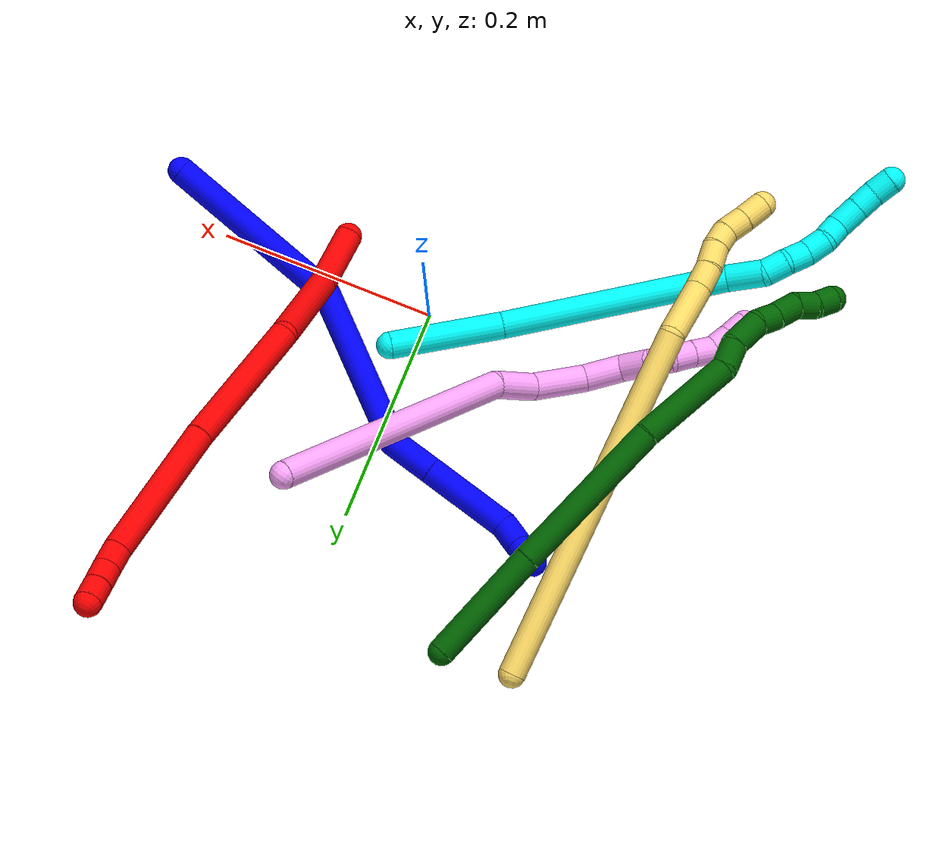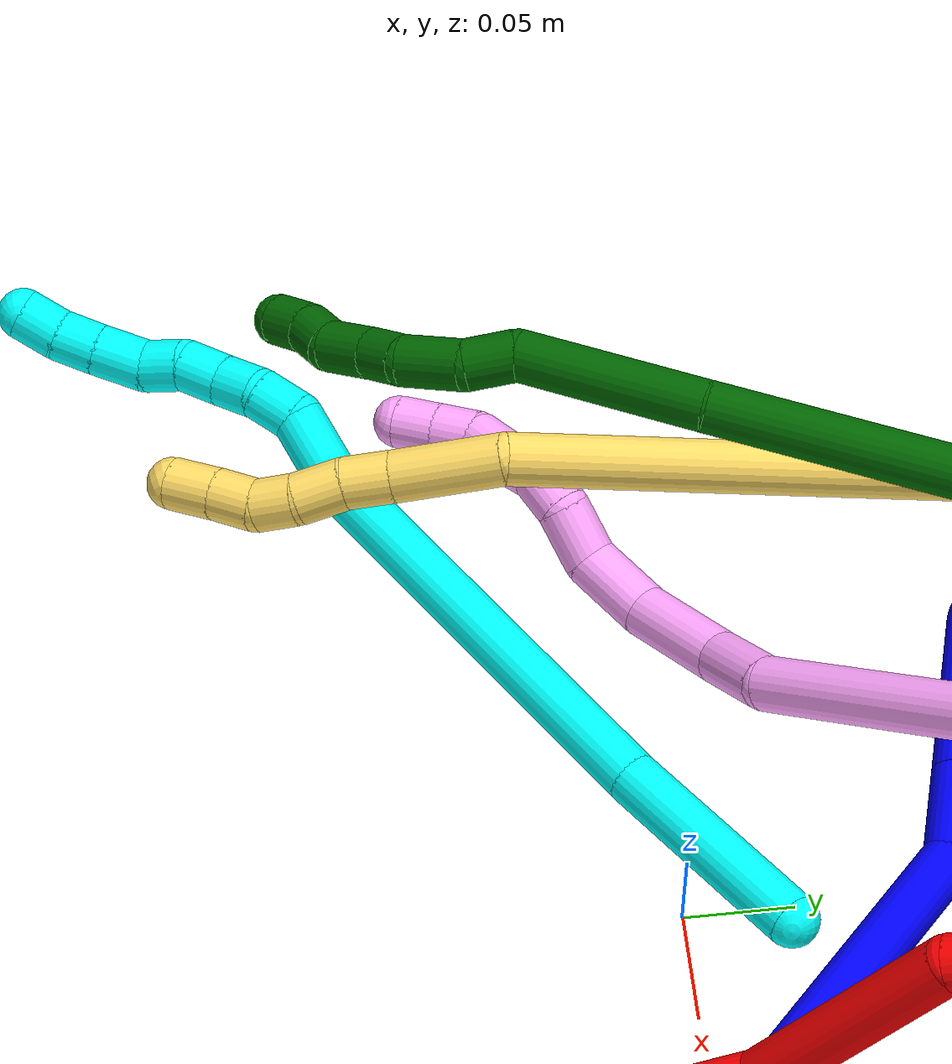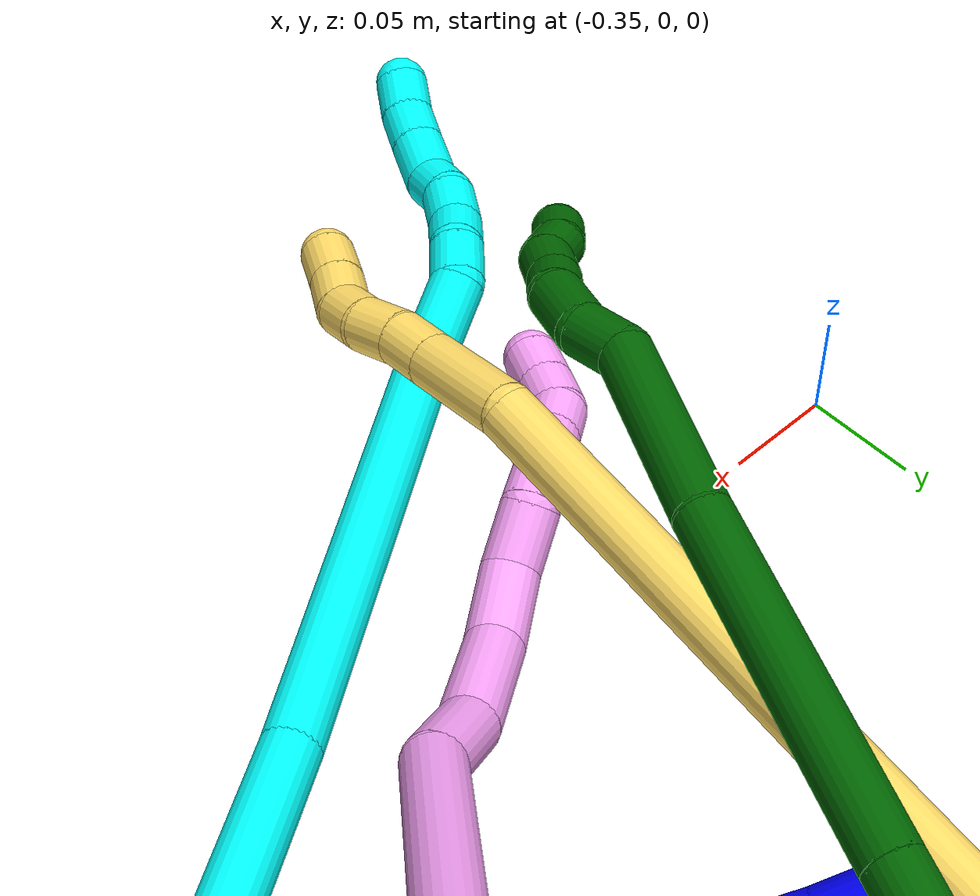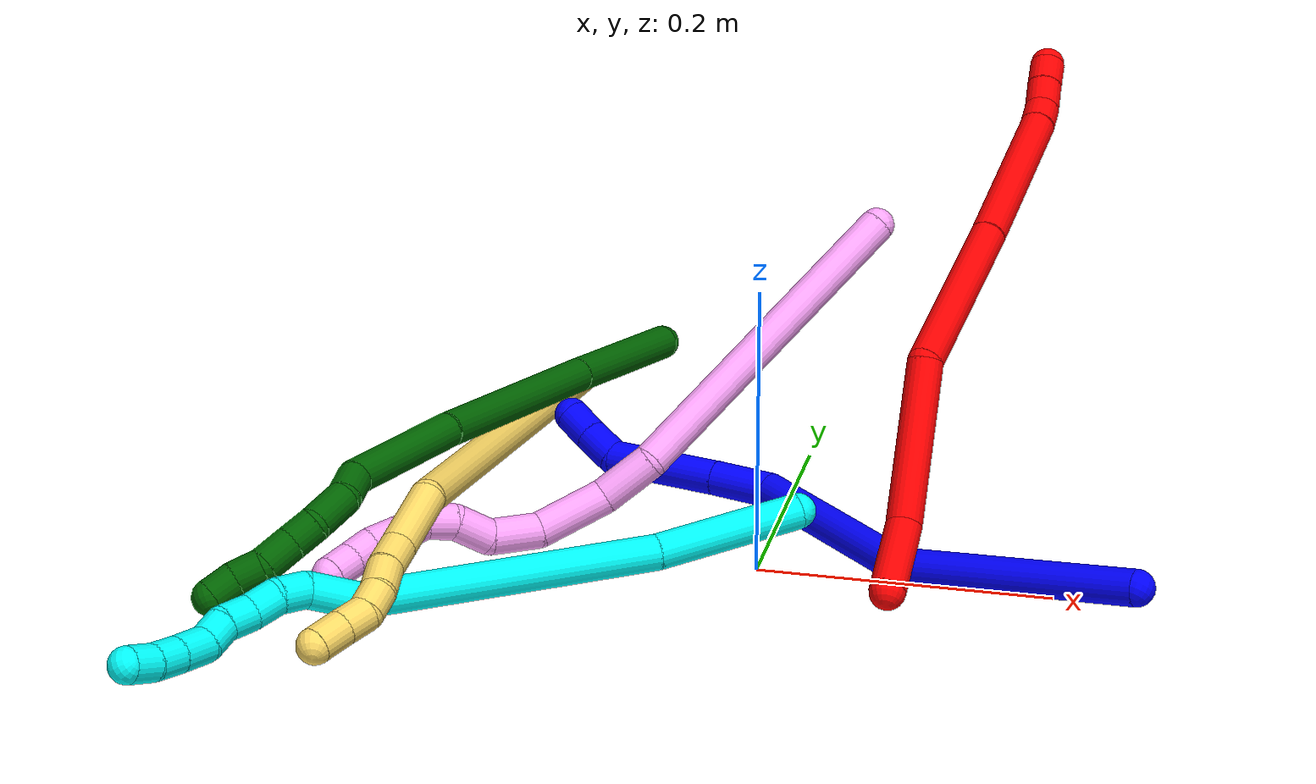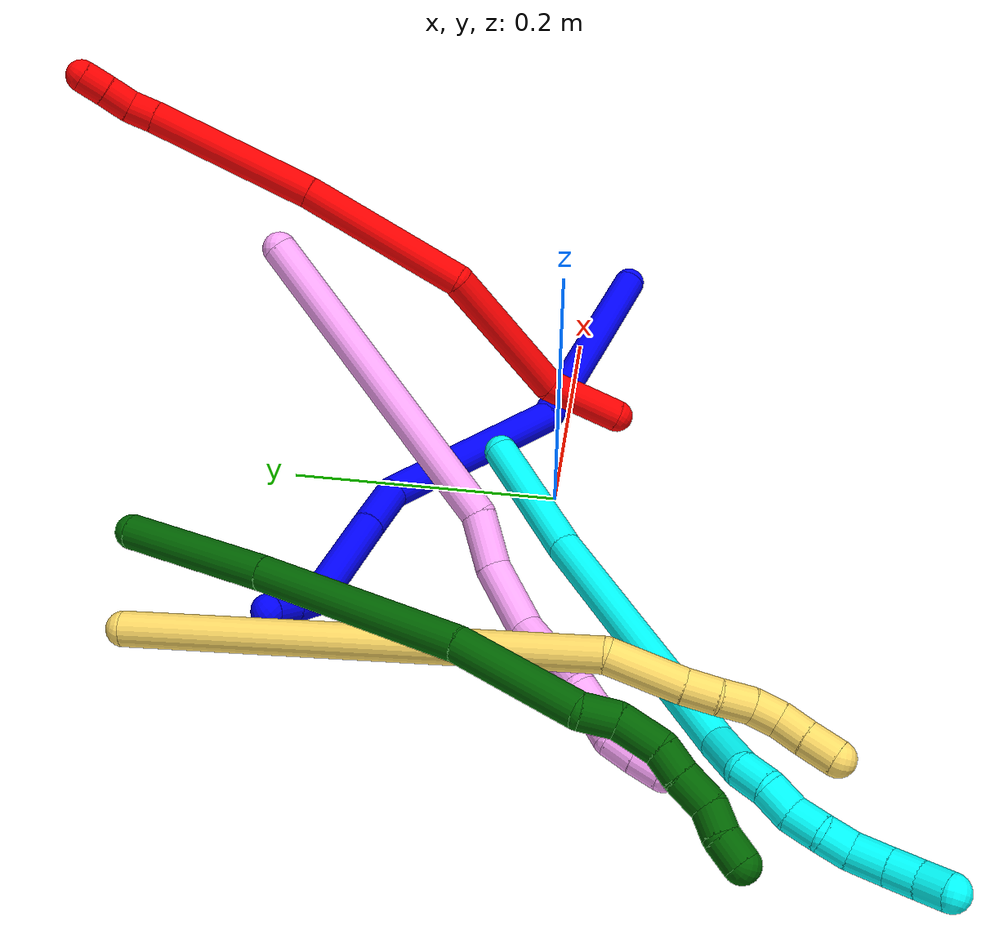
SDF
<sdf version="1.7">
 <world name="default">
  <plugin name="TubeGeneratorPlugin" filename="libtube_generator_plugin.so"/>
  <model name="photoneo_s_sensor">
   <static>1</static>
   <pose>0 0 2 1.57079 1.57079 3.14159</pose>
   <link name="link">
    <inertial><mass>0.1</mass></inertial>
    <sensor name="sensor" type="depth">
     <update_rate>30</update_rate>
     <camera>
      <horizontal_fov>1.22</horizontal_fov>
      <image><width>1920</width><height>1200</height><format>B8G8R8</format></image>
      <clip><near>0.1</near><far>4</far></clip>
      <depth_camera><output>points</output></depth_camera>
     </camera>
     <plugin name="camera_plugin" filename="libgazebo_ros_depth_camera.so">
      <baseline>0.2</baseline>
      <alwaysOn>1</alwaysOn>
      <updateRate>0.0</updateRate>
      <cameraName>camera_ir</cameraName>
      <imageTopicName>/camera/color/image_raw</imageTopicName>
      <cameraInfoTopicName>/camera/color/camera_info</cameraInfoTopicName>
      <depthImageTopicName>/camera/depth/image_raw</depthImageTopicName>
      <depthImageCameraInfoTopicName>/camera/depth/camera_info</depthImageCameraInfoTopicName>
      <pointCloudTopicName>/camera/depth/points</pointCloudTopicName>
      <frameName>fr_optical</frameName>
      <pointCloudCutoff>0.1</pointCloudCutoff>
      <pointCloudCutoffMax>2.0</pointCloudCutoffMax>
      <distortionK1>0</distortionK1>
      <distortionK2>0</distortionK2>
      <distortionK3>0</distortionK3>
      <distortionT1>0</distortionT1>
      <distortionT2>0</distortionT2>
      <CxPrime>0</CxPrime>
      <Cx>0</Cx>
      <Cy>0</Cy>
      <focalLength>0</focalLength>
      <hackBaseline>0</hackBaseline>
     </plugin>
    </sensor>
   </link>
  </model>
  <gravity>0 0 -9.8</gravity>
  <magnetic_field>6e-06 2.3e-05 -4.2e-05</magnetic_field>
  <atmosphere type="adiabatic"/>
  <physics name="default_physics" default="0" type="ode">
   <max_step_size>0.003</max_step_size>
   <real_time_factor>1</real_time_factor>
   <real_time_update_rate>1000</real_time_update_rate>
   <max_contacts>10000</max_contacts>
   <ode>
    <solver>
     <type>quick</type>
     <iters>100</iters>
     <sor>1.3</sor>
     <use_dynamic_moi_rescaling>0</use_dynamic_moi_rescaling>
    </solver>
    <constraints>
     <contact_max_correcting_vel>0</contact_max_correcting_vel>
     <contact_surface_layer>0.001</contact_surface_layer>
     <cfm>0</cfm>
     <erp>0.2</erp>
    </constraints>
   </ode>
  </physics>
  <scene><ambient>0.4 0.4 0.4 1</ambient><background>0.7 0.7 0.7 1</background><shadows>0</shadows></scene>
  <audio><device>default</device></audio>
  <spherical_coordinates>
   <surface_model>EARTH_WGS84</surface_model>
   <latitude_deg>0</latitude_deg>
   <longitude_deg>0</longitude_deg>
   <elevation>0</elevation>
   <heading_deg>0</heading_deg>
  </spherical_coordinates>
  <model name="bin">
   <static>1</static>
   <link name="bottom">
    <collision name="collision-bottom">
     <pose>0 0 -0.01 0 -0 0</pose>
     <geometry><box><size>0.8 0.6 0.02</size></box></geometry>
     <surface>
      <friction><ode><mu>100</mu><mu2>100</mu2></ode></friction>
      <contact><collide_bitmask>65535</collide_bitmask></contact>
     </surface>
    </collision>
   </link>
   <link name="west_wall">
    <collision name="collision-west_wall">
     <pose>-0.41 0 0.1 0 -0 0</pose>
     <geometry><box><size>0.02 0.6 0.2</size></box></geometry>
     <surface>
      <friction><ode><mu>100</mu><mu2>100</mu2></ode></friction>
      <contact><collide_bitmask>65535</collide_bitmask></contact>
     </surface>
    </collision>
   </link>
   <link name="east_wall">
    <collision name="collision-east_wall">
     <pose>0.41 0 0.1 0 -0 0</pose>
     <geometry><box><size>0.02 0.6 0.2</size></box></geometry>
     <surface>
      <friction><ode><mu>100</mu><mu2>100</mu2></ode></friction>
      <contact><collide_bitmask>65535</collide_bitmask></contact>
     </surface>
    </collision>
   </link>
   <link name="south_wall">
    <collision name="collision-south_wall">
     <pose>0 -0.31 0.1 0 -0 0</pose>
     <geometry><box><size>0.8 0.02 0.2</size></box></geometry>
     <surface>
      <friction><ode><mu>100</mu><mu2>100</mu2></ode></friction>
      <contact><collide_bitmask>65535</collide_bitmask></contact>
     </surface>
    </collision>
   </link>
   <link name="north_wall">
    <collision name="collision-north_wall">
     <pose>0 0.31 0.1 0 -0 0</pose>
     <geometry><box><size>0.8 0.02 0.2</size></box></geometry>
     <surface>
      <friction><ode><mu>100</mu><mu2>100</mu2></ode></friction>
      <contact><collide_bitmask>65535</collide_bitmask></contact>
     </surface>
    </collision>
   </link>
  </model>
  <model name="1">
   <static>0</static>
   <link name="1">
    <collision name="collision-cylinder-e_1_1_4">
     <pose>-0.078314 0.033457 -0.013415 -1.95212 -1.13943 1.51633</pose>
     <geometry><cylinder><radius>0.0125</radius><length>0.172424</length></cylinder></geometry>
     <surface>
      <friction><ode><mu>1.16</mu><mu2>1.16</mu2><slip1>0</slip1><slip2>0</slip2></ode></friction>
      <contact><ode><kp>1e+06</kp><kd>1</kd><max_vel>0</max_vel><min_depth>0.001</min_depth></ode></contact>
     </surface>
    </collision>
    <visual name="visual-cylinder-e_1_1_4">
     <pose>-0.078314 0.033457 -0.013415 -1.95212 -1.13943 1.51633</pose>
     <geometry><cylinder><radius>0.0125</radius><length>0.172424</length></cylinder></geometry>
     <material><ambient>0 0 1 1</ambient></material>
    </visual>
    <collision name="collision-cylinder-e_2_4_5">
     <pose>-0.215587 0.110437 -0.006662 -1.13688 -0.887823 0.589842</pose>
     <geometry><cylinder><radius>0.0125</radius><length>0.152012</length></cylinder></geometry>
     <surface>
      <friction><ode><mu>1.16</mu><mu2>1.16</mu2><slip1>0</slip1><slip2>0</slip2></ode></friction>
      <contact><ode><kp>1e+06</kp><kd>1</kd><max_vel>0</max_vel><min_depth>0.001</min_depth></ode></contact>
     </surface>
    </collision>
    <visual name="visual-cylinder-e_2_4_5">
     <pose>-0.215587 0.110437 -0.006662 -1.13688 -0.887823 0.589842</pose>
     <geometry><cylinder><radius>0.0125</radius><length>0.152012</length></cylinder></geometry>
     <material><ambient>0 0 1 1</ambient></material>
    </visual>
    <collision name="collision-cylinder-e_3_5_6">
     <pose>-0.295203 0.159444 0.011893 -1.85656 -1.30086 1.58725</pose>
     <geometry><cylinder><radius>0.0125</radius><length>0.042869</length></cylinder></geometry>
     <surface>
      <friction><ode><mu>1.16</mu><mu2>1.16</mu2><slip1>0</slip1><slip2>0</slip2></ode></friction>
      <contact><ode><kp>1e+06</kp><kd>1</kd><max_vel>0</max_vel><min_depth>0.001</min_depth></ode></contact>
     </surface>
    </collision>
    <visual name="visual-cylinder-e_3_5_6">
     <pose>-0.295203 0.159444 0.011893 -1.85656 -1.30086 1.58725</pose>
     <geometry><cylinder><radius>0.0125</radius><length>0.042869</length></cylinder></geometry>
     <material><ambient>0 0 1 1</ambient></material>
    </visual>
    <collision name="collision-cylinder-e_4_6_7">
     <pose>-0.355576 0.176206 0.006402 -1.90216 -1.27905 1.61241</pose>
     <geometry><cylinder><radius>0.0125</radius><length>0.082933</length></cylinder></geometry>
     <surface>
      <friction><ode><mu>1.16</mu><mu2>1.16</mu2><slip1>0</slip1><slip2>0</slip2></ode></friction>
      <contact><ode><kp>1e+06</kp><kd>1</kd><max_vel>0</max_vel><min_depth>0.001</min_depth></ode></contact>
     </surface>
    </collision>
    <visual name="visual-cylinder-e_4_6_7">
     <pose>-0.355576 0.176206 0.006402 -1.90216 -1.27905 1.61241</pose>
     <geometry><cylinder><radius>0.0125</radius><length>0.082933</length></cylinder></geometry>
     <material><ambient>0 0 1 1</ambient></material>
    </visual>
    <collision name="collision-cylinder-e_5_7_8">
     <pose>-0.407197 0.190166 0.007751 -0.473837 -1.11223 0.297927</pose>
     <geometry><cylinder><radius>0.0125</radius><length>0.026556</length></cylinder></geometry>
     <surface>
      <friction><ode><mu>1.16</mu><mu2>1.16</mu2><slip1>0</slip1><slip2>0</slip2></ode></friction>
      <contact><ode><kp>1e+06</kp><kd>1</kd><max_vel>0</max_vel><min_depth>0.001</min_depth></ode></contact>
     </surface>
    </collision>
    <visual name="visual-cylinder-e_5_7_8">
     <pose>-0.407197 0.190166 0.007751 -0.473837 -1.11223 0.297927</pose>
     <geometry><cylinder><radius>0.0125</radius><length>0.026556</length></cylinder></geometry>
     <material><ambient>0 0 1 1</ambient></material>
    </visual>
    <collision name="collision-cylinder-e_6_8_2">
     <pose>-0.429517 0.194251 0.017901 -0.277853 -1.1142 0.173762</pose>
     <geometry><cylinder><radius>0.0125</radius><length>0.023205</length></cylinder></geometry>
     <surface>
      <friction><ode><mu>1.16</mu><mu2>1.16</mu2><slip1>0</slip1><slip2>0</slip2></ode></friction>
      <contact><ode><kp>1e+06</kp><kd>1</kd><max_vel>0</max_vel><min_depth>0.001</min_depth></ode></contact>
     </surface>
    </collision>
    <visual name="visual-cylinder-e_6_8_2">
     <pose>-0.429517 0.194251 0.017901 -0.277853 -1.1142 0.173762</pose>
     <geometry><cylinder><radius>0.0125</radius><length>0.023205</length></cylinder></geometry>
     <material><ambient>0 0 1 1</ambient></material>
    </visual>
    <collision name="collision-sphere-2">
     <pose>-0.439931 0.195655 0.02282 0 -0 0</pose>
     <geometry><sphere><radius>0.0125</radius></sphere></geometry>
     <surface>
      <friction><ode><mu>1.16</mu><mu2>1.16</mu2><slip1>0</slip1><slip2>0</slip2></ode></friction>
      <contact><ode><kp>1e+06</kp><kd>1</kd><max_vel>0</max_vel><min_depth>0.001</min_depth></ode></contact>
     </surface>
    </collision>
    <visual name="visual-sphere-2">
     <pose>-0.439931 0.195655 0.02282 0 -0 0</pose>
     <geometry><sphere><radius>0.0125</radius></sphere></geometry>
     <material><ambient>0 0 1 1</ambient></material>
    </visual>
    <collision name="collision-sphere-4">
     <pose>-0.156629 0.066915 -0.026829 0 -0 0</pose>
     <geometry><sphere><radius>0.0125</radius></sphere></geometry>
     <surface>
      <friction><ode><mu>1.16</mu><mu2>1.16</mu2><slip1>0</slip1><slip2>0</slip2></ode></friction>
      <contact><ode><kp>1e+06</kp><kd>1</kd><max_vel>0</max_vel><min_depth>0.001</min_depth></ode></contact>
     </surface>
    </collision>
    <visual name="visual-sphere-4">
     <pose>-0.156629 0.066915 -0.026829 0 -0 0</pose>
     <geometry><sphere><radius>0.0125</radius></sphere></geometry>
     <material><ambient>0 0 1 1</ambient></material>
    </visual>
    <collision name="collision-sphere-1">
     <geometry><sphere><radius>0.0125</radius></sphere></geometry>
     <surface>
      <friction><ode><mu>1.16</mu><mu2>1.16</mu2><slip1>0</slip1><slip2>0</slip2></ode></friction>
      <contact><ode><kp>1e+06</kp><kd>1</kd><max_vel>0</max_vel><min_depth>0.001</min_depth></ode></contact>
     </surface>
    </collision>
    <visual name="visual-sphere-1">
     <geometry><sphere><radius>0.0125</radius></sphere></geometry>
     <material><ambient>0 0 1 1</ambient></material>
    </visual>
    <collision name="collision-sphere-8">
     <pose>-0.419103 0.192848 0.012982 0 -0 0</pose>
     <geometry><sphere><radius>0.0125</radius></sphere></geometry>
     <surface>
      <friction><ode><mu>1.16</mu><mu2>1.16</mu2><slip1>0</slip1><slip2>0</slip2></ode></friction>
      <contact><ode><kp>1e+06</kp><kd>1</kd><max_vel>0</max_vel><min_depth>0.001</min_depth></ode></contact>
     </surface>
    </collision>
    <visual name="visual-sphere-8">
     <pose>-0.419103 0.192848 0.012982 0 -0 0</pose>
     <geometry><sphere><radius>0.0125</radius></sphere></geometry>
     <material><ambient>0 0 1 1</ambient></material>
    </visual>
    <collision name="collision-sphere-5">
     <pose>-0.274545 0.15396 0.013504 0 -0 0</pose>
     <geometry><sphere><radius>0.0125</radius></sphere></geometry>
     <surface>
      <friction><ode><mu>1.16</mu><mu2>1.16</mu2><slip1>0</slip1><slip2>0</slip2></ode></friction>
      <contact><ode><kp>1e+06</kp><kd>1</kd><max_vel>0</max_vel><min_depth>0.001</min_depth></ode></contact>
     </surface>
    </collision>
    <visual name="visual-sphere-5">
     <pose>-0.274545 0.15396 0.013504 0 -0 0</pose>
     <geometry><sphere><radius>0.0125</radius></sphere></geometry>
     <material><ambient>0 0 1 1</ambient></material>
    </visual>
    <collision name="collision-sphere-6">
     <pose>-0.315862 0.164928 0.010282 0 -0 0</pose>
     <geometry><sphere><radius>0.0125</radius></sphere></geometry>
     <surface>
      <friction><ode><mu>1.16</mu><mu2>1.16</mu2><slip1>0</slip1><slip2>0</slip2></ode></friction>
      <contact><ode><kp>1e+06</kp><kd>1</kd><max_vel>0</max_vel><min_depth>0.001</min_depth></ode></contact>
     </surface>
    </collision>
    <visual name="visual-sphere-6">
     <pose>-0.315862 0.164928 0.010282 0 -0 0</pose>
     <geometry><sphere><radius>0.0125</radius></sphere></geometry>
     <material><ambient>0 0 1 1</ambient></material>
    </visual>
    <collision name="collision-sphere-7">
     <pose>-0.39529 0.187484 0.002521 0 -0 0</pose>
     <geometry><sphere><radius>0.0125</radius></sphere></geometry>
     <surface>
      <friction><ode><mu>1.16</mu><mu2>1.16</mu2><slip1>0</slip1><slip2>0</slip2></ode></friction>
      <contact><ode><kp>1e+06</kp><kd>1</kd><max_vel>0</max_vel><min_depth>0.001</min_depth></ode></contact>
     </surface>
    </collision>
    <visual name="visual-sphere-7">
     <pose>-0.39529 0.187484 0.002521 0 -0 0</pose>
     <geometry><sphere><radius>0.0125</radius></sphere></geometry>
     <material><ambient>0 0 1 1</ambient></material>
    </visual>
    <inertial>
     <pose>-0.2184 0.107126 -0.003328 0 -0 0</pose>
     <mass>0.5</mass>
     <inertia>
      <ixx>0.000437</ixx>
      <ixy>0</ixy>
      <ixz>0</ixz>
      <iyy>0.000955</iyy>
      <iyz>0</iyz>
      <izz>0.000332</izz>
     </inertia>
    </inertial>
   </link>
   <pose>0.257367 -0.034937 0.029815 -0.766091 0.251937 -0.130501</pose>
  </model>
  <model name="2">
   <static>0</static>
   <link name="2">
    <collision name="collision-cylinder-e_1_1_4">
     <pose>-0.006319 0.003725 0.029011 -0.127688 -0.212781 0.013655</pose>
     <geometry><cylinder><radius>0.0125</radius><length>0.059849</length></cylinder></geometry>
     <surface>
      <friction><ode><mu>1.16</mu><mu2>1.16</mu2><slip1>0</slip1><slip2>0</slip2></ode></friction>
      <contact><ode><kp>1e+06</kp><kd>1</kd><max_vel>0</max_vel><min_depth>0.001</min_depth></ode></contact>
     </surface>
    </collision>
    <visual name="visual-cylinder-e_1_1_4">
     <pose>-0.006319 0.003725 0.029011 -0.127688 -0.212781 0.013655</pose>
     <geometry><cylinder><radius>0.0125</radius><length>0.059849</length></cylinder></geometry>
     <material><ambient>1 0 0 1</ambient></material>
    </visual>
    <collision name="collision-cylinder-e_2_4_5">
     <pose>0.000409 0.001152 0.114146 0.111743 0.227043 0.012753</pose>
     <geometry><cylinder><radius>0.0125</radius><length>0.115927</length></cylinder></geometry>
     <surface>
      <friction><ode><mu>1.16</mu><mu2>1.16</mu2><slip1>0</slip1><slip2>0</slip2></ode></friction>
      <contact><ode><kp>1e+06</kp><kd>1</kd><max_vel>0</max_vel><min_depth>0.001</min_depth></ode></contact>
     </surface>
    </collision>
    <visual name="visual-cylinder-e_2_4_5">
     <pose>0.000409 0.001152 0.114146 0.111743 0.227043 0.012753</pose>
     <geometry><cylinder><radius>0.0125</radius><length>0.115927</length></cylinder></geometry>
     <material><ambient>1 0 0 1</ambient></material>
    </visual>
    <collision name="collision-cylinder-e_3_5_6">
     <pose>0.005369 0.012099 0.233228 -0.267348 -0.123259 0.016596</pose>
     <geometry><cylinder><radius>0.0125</radius><length>0.131552</length></cylinder></geometry>
     <surface>
      <friction><ode><mu>1.16</mu><mu2>1.16</mu2><slip1>0</slip1><slip2>0</slip2></ode></friction>
      <contact><ode><kp>1e+06</kp><kd>1</kd><max_vel>0</max_vel><min_depth>0.001</min_depth></ode></contact>
     </surface>
    </collision>
    <visual name="visual-cylinder-e_3_5_6">
     <pose>0.005369 0.012099 0.233228 -0.267348 -0.123259 0.016596</pose>
     <geometry><cylinder><radius>0.0125</radius><length>0.131552</length></cylinder></geometry>
     <material><ambient>1 0 0 1</ambient></material>
    </visual>
    <collision name="collision-cylinder-e_4_6_7">
     <pose>-0.015684 0.04542 0.35806 -0.254214 -0.20011 0.025658</pose>
     <geometry><cylinder><radius>0.0125</radius><length>0.130461</length></cylinder></geometry>
     <surface>
      <friction><ode><mu>1.16</mu><mu2>1.16</mu2><slip1>0</slip1><slip2>0</slip2></ode></friction>
      <contact><ode><kp>1e+06</kp><kd>1</kd><max_vel>0</max_vel><min_depth>0.001</min_depth></ode></contact>
     </surface>
    </collision>
    <visual name="visual-cylinder-e_4_6_7">
     <pose>-0.015684 0.04542 0.35806 -0.254214 -0.20011 0.025658</pose>
     <geometry><cylinder><radius>0.0125</radius><length>0.130461</length></cylinder></geometry>
     <material><ambient>1 0 0 1</ambient></material>
    </visual>
    <collision name="collision-cylinder-e_5_7_8">
     <pose>-0.031136 0.06308 0.429718 -0.160371 -0.245688 0.019842</pose>
     <geometry><cylinder><radius>0.0125</radius><length>0.020436</length></cylinder></geometry>
     <surface>
      <friction><ode><mu>1.16</mu><mu2>1.16</mu2><slip1>0</slip1><slip2>0</slip2></ode></friction>
      <contact><ode><kp>1e+06</kp><kd>1</kd><max_vel>0</max_vel><min_depth>0.001</min_depth></ode></contact>
     </surface>
    </collision>
    <visual name="visual-cylinder-e_5_7_8">
     <pose>-0.031136 0.06308 0.429718 -0.160371 -0.245688 0.019842</pose>
     <geometry><cylinder><radius>0.0125</radius><length>0.020436</length></cylinder></geometry>
     <material><ambient>1 0 0 1</ambient></material>
    </visual>
    <collision name="collision-cylinder-e_6_8_9">
     <pose>-0.034018 0.06439 0.450219 0.025472 -0.03703 -0.000472</pose>
     <geometry><cylinder><radius>0.0125</radius><length>0.021454</length></cylinder></geometry>
     <surface>
      <friction><ode><mu>1.16</mu><mu2>1.16</mu2><slip1>0</slip1><slip2>0</slip2></ode></friction>
      <contact><ode><kp>1e+06</kp><kd>1</kd><max_vel>0</max_vel><min_depth>0.001</min_depth></ode></contact>
     </surface>
    </collision>
    <visual name="visual-cylinder-e_6_8_9">
     <pose>-0.034018 0.06439 0.450219 0.025472 -0.03703 -0.000472</pose>
     <geometry><cylinder><radius>0.0125</radius><length>0.021454</length></cylinder></geometry>
     <material><ambient>1 0 0 1</ambient></material>
    </visual>
    <collision name="collision-cylinder-e_7_9_2">
     <pose>-0.035105 0.064245 0.471071 -0.012662 -0.067921 0.00043</pose>
     <geometry><cylinder><radius>0.0125</radius><length>0.020321</length></cylinder></geometry>
     <surface>
      <friction><ode><mu>1.16</mu><mu2>1.16</mu2><slip1>0</slip1><slip2>0</slip2></ode></friction>
      <contact><ode><kp>1e+06</kp><kd>1</kd><max_vel>0</max_vel><min_depth>0.001</min_depth></ode></contact>
     </surface>
    </collision>
    <visual name="visual-cylinder-e_7_9_2">
     <pose>-0.035105 0.064245 0.471071 -0.012662 -0.067921 0.00043</pose>
     <geometry><cylinder><radius>0.0125</radius><length>0.020321</length></cylinder></geometry>
     <material><ambient>1 0 0 1</ambient></material>
    </visual>
    <collision name="collision-sphere-2">
     <pose>-0.035795 0.064373 0.481208 0 -0 0</pose>
     <geometry><sphere><radius>0.0125</radius></sphere></geometry>
     <surface>
      <friction><ode><mu>1.16</mu><mu2>1.16</mu2><slip1>0</slip1><slip2>0</slip2></ode></friction>
      <contact><ode><kp>1e+06</kp><kd>1</kd><max_vel>0</max_vel><min_depth>0.001</min_depth></ode></contact>
     </surface>
    </collision>
    <visual name="visual-sphere-2">
     <pose>-0.035795 0.064373 0.481208 0 -0 0</pose>
     <geometry><sphere><radius>0.0125</radius></sphere></geometry>
     <material><ambient>1 0 0 1</ambient></material>
    </visual>
    <collision name="collision-sphere-9">
     <pose>-0.034416 0.064117 0.460935 0 -0 0</pose>
     <geometry><sphere><radius>0.0125</radius></sphere></geometry>
     <surface>
      <friction><ode><mu>1.16</mu><mu2>1.16</mu2><slip1>0</slip1><slip2>0</slip2></ode></friction>
      <contact><ode><kp>1e+06</kp><kd>1</kd><max_vel>0</max_vel><min_depth>0.001</min_depth></ode></contact>
     </surface>
    </collision>
    <visual name="visual-sphere-9">
     <pose>-0.034416 0.064117 0.460935 0 -0 0</pose>
     <geometry><sphere><radius>0.0125</radius></sphere></geometry>
     <material><ambient>1 0 0 1</ambient></material>
    </visual>
    <collision name="collision-sphere-4">
     <pose>-0.012639 0.007449 0.058023 0 -0 0</pose>
     <geometry><sphere><radius>0.0125</radius></sphere></geometry>
     <surface>
      <friction><ode><mu>1.16</mu><mu2>1.16</mu2><slip1>0</slip1><slip2>0</slip2></ode></friction>
      <contact><ode><kp>1e+06</kp><kd>1</kd><max_vel>0</max_vel><min_depth>0.001</min_depth></ode></contact>
     </surface>
    </collision>
    <visual name="visual-sphere-4">
     <pose>-0.012639 0.007449 0.058023 0 -0 0</pose>
     <geometry><sphere><radius>0.0125</radius></sphere></geometry>
     <material><ambient>1 0 0 1</ambient></material>
    </visual>
    <collision name="collision-sphere-1">
     <geometry><sphere><radius>0.0125</radius></sphere></geometry>
     <surface>
      <friction><ode><mu>1.16</mu><mu2>1.16</mu2><slip1>0</slip1><slip2>0</slip2></ode></friction>
      <contact><ode><kp>1e+06</kp><kd>1</kd><max_vel>0</max_vel><min_depth>0.001</min_depth></ode></contact>
     </surface>
    </collision>
    <visual name="visual-sphere-1">
     <geometry><sphere><radius>0.0125</radius></sphere></geometry>
     <material><ambient>1 0 0 1</ambient></material>
    </visual>
    <collision name="collision-sphere-8">
     <pose>-0.033621 0.064663 0.439502 0 -0 0</pose>
     <geometry><sphere><radius>0.0125</radius></sphere></geometry>
     <surface>
      <friction><ode><mu>1.16</mu><mu2>1.16</mu2><slip1>0</slip1><slip2>0</slip2></ode></friction>
      <contact><ode><kp>1e+06</kp><kd>1</kd><max_vel>0</max_vel><min_depth>0.001</min_depth></ode></contact>
     </surface>
    </collision>
    <visual name="visual-sphere-8">
     <pose>-0.033621 0.064663 0.439502 0 -0 0</pose>
     <geometry><sphere><radius>0.0125</radius></sphere></geometry>
     <material><ambient>1 0 0 1</ambient></material>
    </visual>
    <collision name="collision-sphere-5">
     <pose>0.013456 -0.005146 0.17027 0 -0 0</pose>
     <geometry><sphere><radius>0.0125</radius></sphere></geometry>
     <surface>
      <friction><ode><mu>1.16</mu><mu2>1.16</mu2><slip1>0</slip1><slip2>0</slip2></ode></friction>
      <contact><ode><kp>1e+06</kp><kd>1</kd><max_vel>0</max_vel><min_depth>0.001</min_depth></ode></contact>
     </surface>
    </collision>
    <visual name="visual-sphere-5">
     <pose>0.013456 -0.005146 0.17027 0 -0 0</pose>
     <geometry><sphere><radius>0.0125</radius></sphere></geometry>
     <material><ambient>1 0 0 1</ambient></material>
    </visual>
    <collision name="collision-sphere-6">
     <pose>-0.002718 0.029343 0.296185 0 -0 0</pose>
     <geometry><sphere><radius>0.0125</radius></sphere></geometry>
     <surface>
      <friction><ode><mu>1.16</mu><mu2>1.16</mu2><slip1>0</slip1><slip2>0</slip2></ode></friction>
      <contact><ode><kp>1e+06</kp><kd>1</kd><max_vel>0</max_vel><min_depth>0.001</min_depth></ode></contact>
     </surface>
    </collision>
    <visual name="visual-sphere-6">
     <pose>-0.002718 0.029343 0.296185 0 -0 0</pose>
     <geometry><sphere><radius>0.0125</radius></sphere></geometry>
     <material><ambient>1 0 0 1</ambient></material>
    </visual>
    <collision name="collision-sphere-7">
     <pose>-0.028651 0.061497 0.419934 0 -0 0</pose>
     <geometry><sphere><radius>0.0125</radius></sphere></geometry>
     <surface>
      <friction><ode><mu>1.16</mu><mu2>1.16</mu2><slip1>0</slip1><slip2>0</slip2></ode></friction>
      <contact><ode><kp>1e+06</kp><kd>1</kd><max_vel>0</max_vel><min_depth>0.001</min_depth></ode></contact>
     </surface>
    </collision>
    <visual name="visual-sphere-7">
     <pose>-0.028651 0.061497 0.419934 0 -0 0</pose>
     <geometry><sphere><radius>0.0125</radius></sphere></geometry>
     <material><ambient>1 0 0 1</ambient></material>
    </visual>
    <inertial>
     <pose>-0.007501 0.023699 0.240754 0 -0 0</pose>
     <mass>0.5</mass>
     <inertia>
      <ixx>0.000542</ixx>
      <ixy>0</ixy>
      <ixz>0</ixz>
      <iyy>0.000545</iyy>
      <iyz>0</iyz>
      <izz>-1.2e-05</izz>
     </inertia>
    </inertial>
   </link>
   <pose>0.095278 -0.038539 0.011498 -0.52923 -0.797329 -0.896157</pose>
  </model>
  <model name="3">
   <static>0</static>
   <link name="3">
    <collision name="collision-cylinder-e_1_1_4">
     <pose>-0.027899 -0.029246 0.033125 0.723285 -0.563164 -0.217981</pose>
     <geometry><cylinder><radius>0.0125</radius><length>0.104517</length></cylinder></geometry>
     <surface>
      <friction><ode><mu>1.16</mu><mu2>1.16</mu2><slip1>0</slip1><slip2>0</slip2></ode></friction>
      <contact><ode><kp>1e+06</kp><kd>1</kd><max_vel>0</max_vel><min_depth>0.001</min_depth></ode></contact>
     </surface>
    </collision>
    <visual name="visual-cylinder-e_1_1_4">
     <pose>-0.027899 -0.029246 0.033125 0.723285 -0.563164 -0.217981</pose>
     <geometry><cylinder><radius>0.0125</radius><length>0.104517</length></cylinder></geometry>
     <material><ambient>0.003922 1 0.996078 1</ambient></material>
    </visual>
    <collision name="collision-cylinder-e_2_4_5">
     <pose>-0.107598 -0.127916 0.124961 0.868806 -0.517866 -0.244561</pose>
     <geometry><cylinder><radius>0.0125</radius><length>0.209284</length></cylinder></geometry>
     <surface>
      <friction><ode><mu>1.16</mu><mu2>1.16</mu2><slip1>0</slip1><slip2>0</slip2></ode></friction>
      <contact><ode><kp>1e+06</kp><kd>1</kd><max_vel>0</max_vel><min_depth>0.001</min_depth></ode></contact>
     </surface>
    </collision>
    <visual name="visual-cylinder-e_2_4_5">
     <pose>-0.107598 -0.127916 0.124961 0.868806 -0.517866 -0.244561</pose>
     <geometry><cylinder><radius>0.0125</radius><length>0.209284</length></cylinder></geometry>
     <material><ambient>0.003922 1 0.996078 1</ambient></material>
    </visual>
    <collision name="collision-cylinder-e_3_5_6">
     <pose>-0.163881 -0.213004 0.191138 1.12604 -0.252772 -0.160053</pose>
     <geometry><cylinder><radius>0.0125</radius><length>0.035845</length></cylinder></geometry>
     <surface>
      <friction><ode><mu>1.16</mu><mu2>1.16</mu2><slip1>0</slip1><slip2>0</slip2></ode></friction>
      <contact><ode><kp>1e+06</kp><kd>1</kd><max_vel>0</max_vel><min_depth>0.001</min_depth></ode></contact>
     </surface>
    </collision>
    <visual name="visual-cylinder-e_3_5_6">
     <pose>-0.163881 -0.213004 0.191138 1.12604 -0.252772 -0.160053</pose>
     <geometry><cylinder><radius>0.0125</radius><length>0.035845</length></cylinder></geometry>
     <material><ambient>0.003922 1 0.996078 1</ambient></material>
    </visual>
    <collision name="collision-cylinder-e_4_6_7">
     <pose>-0.175572 -0.235913 0.202488 1.07871 -0.719942 -0.443158</pose>
     <geometry><cylinder><radius>0.0125</radius><length>0.021866</length></cylinder></geometry>
     <surface>
      <friction><ode><mu>1.16</mu><mu2>1.16</mu2><slip1>0</slip1><slip2>0</slip2></ode></friction>
      <contact><ode><kp>1e+06</kp><kd>1</kd><max_vel>0</max_vel><min_depth>0.001</min_depth></ode></contact>
     </surface>
    </collision>
    <visual name="visual-cylinder-e_4_6_7">
     <pose>-0.175572 -0.235913 0.202488 1.07871 -0.719942 -0.443158</pose>
     <geometry><cylinder><radius>0.0125</radius><length>0.021866</length></cylinder></geometry>
     <material><ambient>0.003922 1 0.996078 1</ambient></material>
    </visual>
    <collision name="collision-cylinder-e_5_7_8">
     <pose>-0.190824 -0.247214 0.212087 0.617237 -0.854057 -0.288121</pose>
     <geometry><cylinder><radius>0.0125</radius><length>0.021338</length></cylinder></geometry>
     <surface>
      <friction><ode><mu>1.16</mu><mu2>1.16</mu2><slip1>0</slip1><slip2>0</slip2></ode></friction>
      <contact><ode><kp>1e+06</kp><kd>1</kd><max_vel>0</max_vel><min_depth>0.001</min_depth></ode></contact>
     </surface>
    </collision>
    <visual name="visual-cylinder-e_5_7_8">
     <pose>-0.190824 -0.247214 0.212087 0.617237 -0.854057 -0.288121</pose>
     <geometry><cylinder><radius>0.0125</radius><length>0.021338</length></cylinder></geometry>
     <material><ambient>0.003922 1 0.996078 1</ambient></material>
    </visual>
    <collision name="collision-cylinder-e_6_8_9">
     <pose>-0.20736 -0.257234 0.221191 1.05399 -0.891377 -0.542297</pose>
     <geometry><cylinder><radius>0.0125</radius><length>0.021831</length></cylinder></geometry>
     <surface>
      <friction><ode><mu>1.16</mu><mu2>1.16</mu2><slip1>0</slip1><slip2>0</slip2></ode></friction>
      <contact><ode><kp>1e+06</kp><kd>1</kd><max_vel>0</max_vel><min_depth>0.001</min_depth></ode></contact>
     </surface>
    </collision>
    <visual name="visual-cylinder-e_6_8_9">
     <pose>-0.20736 -0.257234 0.221191 1.05399 -0.891377 -0.542297</pose>
     <geometry><cylinder><radius>0.0125</radius><length>0.021831</length></cylinder></geometry>
     <material><ambient>0.003922 1 0.996078 1</ambient></material>
    </visual>
    <collision name="collision-cylinder-e_7_9_10">
     <pose>-0.225322 -0.265188 0.227183 0.653047 -1.23765 -0.473285</pose>
     <geometry><cylinder><radius>0.0125</radius><length>0.020044</length></cylinder></geometry>
     <surface>
      <friction><ode><mu>1.16</mu><mu2>1.16</mu2><slip1>0</slip1><slip2>0</slip2></ode></friction>
      <contact><ode><kp>1e+06</kp><kd>1</kd><max_vel>0</max_vel><min_depth>0.001</min_depth></ode></contact>
     </surface>
    </collision>
    <visual name="visual-cylinder-e_7_9_10">
     <pose>-0.225322 -0.265188 0.227183 0.653047 -1.23765 -0.473285</pose>
     <geometry><cylinder><radius>0.0125</radius><length>0.020044</length></cylinder></geometry>
     <material><ambient>0.003922 1 0.996078 1</ambient></material>
    </visual>
    <collision name="collision-cylinder-e_8_10_11">
     <pose>-0.244805 -0.274419 0.231581 1.32776 -0.930547 -0.748505</pose>
     <geometry><cylinder><radius>0.0125</radius><length>0.024969</length></cylinder></geometry>
     <surface>
      <friction><ode><mu>1.16</mu><mu2>1.16</mu2><slip1>0</slip1><slip2>0</slip2></ode></friction>
      <contact><ode><kp>1e+06</kp><kd>1</kd><max_vel>0</max_vel><min_depth>0.001</min_depth></ode></contact>
     </surface>
    </collision>
    <visual name="visual-cylinder-e_8_10_11">
     <pose>-0.244805 -0.274419 0.231581 1.32776 -0.930547 -0.748505</pose>
     <geometry><cylinder><radius>0.0125</radius><length>0.024969</length></cylinder></geometry>
     <material><ambient>0.003922 1 0.996078 1</ambient></material>
    </visual>
    <collision name="collision-cylinder-e_9_11_12">
     <pose>-0.262705 -0.287817 0.234717 1.35639 -0.896566 -0.739338</pose>
     <geometry><cylinder><radius>0.0125</radius><length>0.020194</length></cylinder></geometry>
     <surface>
      <friction><ode><mu>1.16</mu><mu2>1.16</mu2><slip1>0</slip1><slip2>0</slip2></ode></friction>
      <contact><ode><kp>1e+06</kp><kd>1</kd><max_vel>0</max_vel><min_depth>0.001</min_depth></ode></contact>
     </surface>
    </collision>
    <visual name="visual-cylinder-e_9_11_12">
     <pose>-0.262705 -0.287817 0.234717 1.35639 -0.896566 -0.739338</pose>
     <geometry><cylinder><radius>0.0125</radius><length>0.020194</length></cylinder></geometry>
     <material><ambient>0.003922 1 0.996078 1</ambient></material>
    </visual>
    <collision name="collision-cylinder-e_10_12_2">
     <pose>-0.277227 -0.301409 0.237421 1.38942 -0.720491 -0.608292</pose>
     <geometry><cylinder><radius>0.0125</radius><length>0.020113</length></cylinder></geometry>
     <surface>
      <friction><ode><mu>1.16</mu><mu2>1.16</mu2><slip1>0</slip1><slip2>0</slip2></ode></friction>
      <contact><ode><kp>1e+06</kp><kd>1</kd><max_vel>0</max_vel><min_depth>0.001</min_depth></ode></contact>
     </surface>
    </collision>
    <visual name="visual-cylinder-e_10_12_2">
     <pose>-0.277227 -0.301409 0.237421 1.38942 -0.720491 -0.608292</pose>
     <geometry><cylinder><radius>0.0125</radius><length>0.020113</length></cylinder></geometry>
     <material><ambient>0.003922 1 0.996078 1</ambient></material>
    </visual>
    <collision name="collision-sphere-2">
     <pose>-0.283862 -0.308842 0.238785 0 -0 0</pose>
     <geometry><sphere><radius>0.0125</radius></sphere></geometry>
     <surface>
      <friction><ode><mu>1.16</mu><mu2>1.16</mu2><slip1>0</slip1><slip2>0</slip2></ode></friction>
      <contact><ode><kp>1e+06</kp><kd>1</kd><max_vel>0</max_vel><min_depth>0.001</min_depth></ode></contact>
     </surface>
    </collision>
    <visual name="visual-sphere-2">
     <pose>-0.283862 -0.308842 0.238785 0 -0 0</pose>
     <geometry><sphere><radius>0.0125</radius></sphere></geometry>
     <material><ambient>0.003922 1 0.996078 1</ambient></material>
    </visual>
    <collision name="collision-sphere-12">
     <pose>-0.270592 -0.293976 0.236058 0 -0 0</pose>
     <geometry><sphere><radius>0.0125</radius></sphere></geometry>
     <surface>
      <friction><ode><mu>1.16</mu><mu2>1.16</mu2><slip1>0</slip1><slip2>0</slip2></ode></friction>
      <contact><ode><kp>1e+06</kp><kd>1</kd><max_vel>0</max_vel><min_depth>0.001</min_depth></ode></contact>
     </surface>
    </collision>
    <visual name="visual-sphere-12">
     <pose>-0.270592 -0.293976 0.236058 0 -0 0</pose>
     <geometry><sphere><radius>0.0125</radius></sphere></geometry>
     <material><ambient>0.003922 1 0.996078 1</ambient></material>
    </visual>
    <collision name="collision-sphere-11">
     <pose>-0.254817 -0.281658 0.233376 0 -0 0</pose>
     <geometry><sphere><radius>0.0125</radius></sphere></geometry>
     <surface>
      <friction><ode><mu>1.16</mu><mu2>1.16</mu2><slip1>0</slip1><slip2>0</slip2></ode></friction>
      <contact><ode><kp>1e+06</kp><kd>1</kd><max_vel>0</max_vel><min_depth>0.001</min_depth></ode></contact>
     </surface>
    </collision>
    <visual name="visual-sphere-11">
     <pose>-0.254817 -0.281658 0.233376 0 -0 0</pose>
     <geometry><sphere><radius>0.0125</radius></sphere></geometry>
     <material><ambient>0.003922 1 0.996078 1</ambient></material>
    </visual>
    <collision name="collision-sphere-10">
     <pose>-0.234793 -0.26718 0.229786 0 -0 0</pose>
     <geometry><sphere><radius>0.0125</radius></sphere></geometry>
     <surface>
      <friction><ode><mu>1.16</mu><mu2>1.16</mu2><slip1>0</slip1><slip2>0</slip2></ode></friction>
      <contact><ode><kp>1e+06</kp><kd>1</kd><max_vel>0</max_vel><min_depth>0.001</min_depth></ode></contact>
     </surface>
    </collision>
    <visual name="visual-sphere-10">
     <pose>-0.234793 -0.26718 0.229786 0 -0 0</pose>
     <geometry><sphere><radius>0.0125</radius></sphere></geometry>
     <material><ambient>0.003922 1 0.996078 1</ambient></material>
    </visual>
    <collision name="collision-sphere-9">
     <pose>-0.215852 -0.263197 0.22458 0 -0 0</pose>
     <geometry><sphere><radius>0.0125</radius></sphere></geometry>
     <surface>
      <friction><ode><mu>1.16</mu><mu2>1.16</mu2><slip1>0</slip1><slip2>0</slip2></ode></friction>
      <contact><ode><kp>1e+06</kp><kd>1</kd><max_vel>0</max_vel><min_depth>0.001</min_depth></ode></contact>
     </surface>
    </collision>
    <visual name="visual-sphere-9">
     <pose>-0.215852 -0.263197 0.22458 0 -0 0</pose>
     <geometry><sphere><radius>0.0125</radius></sphere></geometry>
     <material><ambient>0.003922 1 0.996078 1</ambient></material>
    </visual>
    <collision name="collision-sphere-4">
     <pose>-0.055798 -0.058492 0.06625 0 -0 0</pose>
     <geometry><sphere><radius>0.0125</radius></sphere></geometry>
     <surface>
      <friction><ode><mu>1.16</mu><mu2>1.16</mu2><slip1>0</slip1><slip2>0</slip2></ode></friction>
      <contact><ode><kp>1e+06</kp><kd>1</kd><max_vel>0</max_vel><min_depth>0.001</min_depth></ode></contact>
     </surface>
    </collision>
    <visual name="visual-sphere-4">
     <pose>-0.055798 -0.058492 0.06625 0 -0 0</pose>
     <geometry><sphere><radius>0.0125</radius></sphere></geometry>
     <material><ambient>0.003922 1 0.996078 1</ambient></material>
    </visual>
    <collision name="collision-sphere-1">
     <geometry><sphere><radius>0.0125</radius></sphere></geometry>
     <surface>
      <friction><ode><mu>1.16</mu><mu2>1.16</mu2><slip1>0</slip1><slip2>0</slip2></ode></friction>
      <contact><ode><kp>1e+06</kp><kd>1</kd><max_vel>0</max_vel><min_depth>0.001</min_depth></ode></contact>
     </surface>
    </collision>
    <visual name="visual-sphere-1">
     <geometry><sphere><radius>0.0125</radius></sphere></geometry>
     <material><ambient>0.003922 1 0.996078 1</ambient></material>
    </visual>
    <collision name="collision-sphere-8">
     <pose>-0.198868 -0.251271 0.217802 0 -0 0</pose>
     <geometry><sphere><radius>0.0125</radius></sphere></geometry>
     <surface>
      <friction><ode><mu>1.16</mu><mu2>1.16</mu2><slip1>0</slip1><slip2>0</slip2></ode></friction>
      <contact><ode><kp>1e+06</kp><kd>1</kd><max_vel>0</max_vel><min_depth>0.001</min_depth></ode></contact>
     </surface>
    </collision>
    <visual name="visual-sphere-8">
     <pose>-0.198868 -0.251271 0.217802 0 -0 0</pose>
     <geometry><sphere><radius>0.0125</radius></sphere></geometry>
     <material><ambient>0.003922 1 0.996078 1</ambient></material>
    </visual>
    <collision name="collision-sphere-5">
     <pose>-0.159399 -0.197339 0.183673 0 -0 0</pose>
     <geometry><sphere><radius>0.0125</radius></sphere></geometry>
     <surface>
      <friction><ode><mu>1.16</mu><mu2>1.16</mu2><slip1>0</slip1><slip2>0</slip2></ode></friction>
      <contact><ode><kp>1e+06</kp><kd>1</kd><max_vel>0</max_vel><min_depth>0.001</min_depth></ode></contact>
     </surface>
    </collision>
    <visual name="visual-sphere-5">
     <pose>-0.159399 -0.197339 0.183673 0 -0 0</pose>
     <geometry><sphere><radius>0.0125</radius></sphere></geometry>
     <material><ambient>0.003922 1 0.996078 1</ambient></material>
    </visual>
    <collision name="collision-sphere-6">
     <pose>-0.168363 -0.228669 0.198604 0 -0 0</pose>
     <geometry><sphere><radius>0.0125</radius></sphere></geometry>
     <surface>
      <friction><ode><mu>1.16</mu><mu2>1.16</mu2><slip1>0</slip1><slip2>0</slip2></ode></friction>
      <contact><ode><kp>1e+06</kp><kd>1</kd><max_vel>0</max_vel><min_depth>0.001</min_depth></ode></contact>
     </surface>
    </collision>
    <visual name="visual-sphere-6">
     <pose>-0.168363 -0.228669 0.198604 0 -0 0</pose>
     <geometry><sphere><radius>0.0125</radius></sphere></geometry>
     <material><ambient>0.003922 1 0.996078 1</ambient></material>
    </visual>
    <collision name="collision-sphere-7">
     <pose>-0.182781 -0.243158 0.206372 0 -0 0</pose>
     <geometry><sphere><radius>0.0125</radius></sphere></geometry>
     <surface>
      <friction><ode><mu>1.16</mu><mu2>1.16</mu2><slip1>0</slip1><slip2>0</slip2></ode></friction>
      <contact><ode><kp>1e+06</kp><kd>1</kd><max_vel>0</max_vel><min_depth>0.001</min_depth></ode></contact>
     </surface>
    </collision>
    <visual name="visual-sphere-7">
     <pose>-0.182781 -0.243158 0.206372 0 -0 0</pose>
     <geometry><sphere><radius>0.0125</radius></sphere></geometry>
     <material><ambient>0.003922 1 0.996078 1</ambient></material>
    </visual>
    <inertial>
     <pose>-0.130512 -0.155107 0.140198 0 -0 0</pose>
     <mass>0.5</mass>
     <inertia>
      <ixx>0.000537</ixx>
      <ixy>0</ixy>
      <ixz>0</ixz>
      <iyy>0.000436</iyy>
      <iyz>0</iyz>
      <izz>0.001043</izz>
     </inertia>
    </inertial>
   </link>
   <pose>0.019708 0.044043 0.025858 -2.23863 -0.335309 1.61275</pose>
  </model>
  <model name="4">
   <static>0</static>
   <link name="4">
    <collision name="collision-cylinder-e_1_1_4">
     <pose>-0.093285 0.011108 -0.077334 -2.99894 -0.873592 2.83788</pose>
     <geometry><cylinder><radius>0.0125</radius><length>0.24336</length></cylinder></geometry>
     <surface>
      <friction><ode><mu>1.16</mu><mu2>1.16</mu2><slip1>0</slip1><slip2>0</slip2></ode></friction>
      <contact><ode><kp>1e+06</kp><kd>1</kd><max_vel>0</max_vel><min_depth>0.001</min_depth></ode></contact>
     </surface>
    </collision>
    <visual name="visual-cylinder-e_1_1_4">
     <pose>-0.093285 0.011108 -0.077334 -2.99894 -0.873592 2.83788</pose>
     <geometry><cylinder><radius>0.0125</radius><length>0.24336</length></cylinder></geometry>
     <material><ambient>1 0.65098 0.996078 1</ambient></material>
    </visual>
    <collision name="collision-cylinder-e_2_4_5">
     <pose>-0.20483 0.019188 -0.16239 2.76788 -1.14448 -2.57061</pose>
     <geometry><cylinder><radius>0.0125</radius><length>0.04011</length></cylinder></geometry>
     <surface>
      <friction><ode><mu>1.16</mu><mu2>1.16</mu2><slip1>0</slip1><slip2>0</slip2></ode></friction>
      <contact><ode><kp>1e+06</kp><kd>1</kd><max_vel>0</max_vel><min_depth>0.001</min_depth></ode></contact>
     </surface>
    </collision>
    <visual name="visual-cylinder-e_2_4_5">
     <pose>-0.20483 0.019188 -0.16239 2.76788 -1.14448 -2.57061</pose>
     <geometry><cylinder><radius>0.0125</radius><length>0.04011</length></cylinder></geometry>
     <material><ambient>1 0.65098 0.996078 1</ambient></material>
    </visual>
    <collision name="collision-cylinder-e_3_5_6">
     <pose>-0.242277 0.0101 -0.186184 2.78107 -0.84057 -2.36722</pose>
     <geometry><cylinder><radius>0.0125</radius><length>0.051506</length></cylinder></geometry>
     <surface>
      <friction><ode><mu>1.16</mu><mu2>1.16</mu2><slip1>0</slip1><slip2>0</slip2></ode></friction>
      <contact><ode><kp>1e+06</kp><kd>1</kd><max_vel>0</max_vel><min_depth>0.001</min_depth></ode></contact>
     </surface>
    </collision>
    <visual name="visual-cylinder-e_3_5_6">
     <pose>-0.242277 0.0101 -0.186184 2.78107 -0.84057 -2.36722</pose>
     <geometry><cylinder><radius>0.0125</radius><length>0.051506</length></cylinder></geometry>
     <material><ambient>1 0.65098 0.996078 1</ambient></material>
    </visual>
    <collision name="collision-cylinder-e_4_6_7">
     <pose>-0.269713 -0.00393 -0.216303 2.62544 -0.472331 -1.47849</pose>
     <geometry><cylinder><radius>0.0125</radius><length>0.036269</length></cylinder></geometry>
     <surface>
      <friction><ode><mu>1.16</mu><mu2>1.16</mu2><slip1>0</slip1><slip2>0</slip2></ode></friction>
      <contact><ode><kp>1e+06</kp><kd>1</kd><max_vel>0</max_vel><min_depth>0.001</min_depth></ode></contact>
     </surface>
    </collision>
    <visual name="visual-cylinder-e_4_6_7">
     <pose>-0.269713 -0.00393 -0.216303 2.62544 -0.472331 -1.47849</pose>
     <geometry><cylinder><radius>0.0125</radius><length>0.036269</length></cylinder></geometry>
     <material><ambient>1 0.65098 0.996078 1</ambient></material>
    </visual>
    <collision name="collision-cylinder-e_5_7_8">
     <pose>-0.278507 -0.021839 -0.239664 2.32383 -0.039879 -0.091983</pose>
     <geometry><cylinder><radius>0.0125</radius><length>0.027268</length></cylinder></geometry>
     <surface>
      <friction><ode><mu>1.16</mu><mu2>1.16</mu2><slip1>0</slip1><slip2>0</slip2></ode></friction>
      <contact><ode><kp>1e+06</kp><kd>1</kd><max_vel>0</max_vel><min_depth>0.001</min_depth></ode></contact>
     </surface>
    </collision>
    <visual name="visual-cylinder-e_5_7_8">
     <pose>-0.278507 -0.021839 -0.239664 2.32383 -0.039879 -0.091983</pose>
     <geometry><cylinder><radius>0.0125</radius><length>0.027268</length></cylinder></geometry>
     <material><ambient>1 0.65098 0.996078 1</ambient></material>
    </visual>
    <collision name="collision-cylinder-e_6_8_9">
     <pose>-0.283234 -0.037827 -0.256472 2.4624 -0.409842 -1.06356</pose>
     <geometry><cylinder><radius>0.0125</radius><length>0.020995</length></cylinder></geometry>
     <surface>
      <friction><ode><mu>1.16</mu><mu2>1.16</mu2><slip1>0</slip1><slip2>0</slip2></ode></friction>
      <contact><ode><kp>1e+06</kp><kd>1</kd><max_vel>0</max_vel><min_depth>0.001</min_depth></ode></contact>
     </surface>
    </collision>
    <visual name="visual-cylinder-e_6_8_9">
     <pose>-0.283234 -0.037827 -0.256472 2.4624 -0.409842 -1.06356</pose>
     <geometry><cylinder><radius>0.0125</radius><length>0.020995</length></cylinder></geometry>
     <material><ambient>1 0.65098 0.996078 1</ambient></material>
    </visual>
    <collision name="collision-cylinder-e_7_9_10">
     <pose>-0.294256 -0.046204 -0.270979 2.82115 -0.746583 -2.3589</pose>
     <geometry><cylinder><radius>0.0125</radius><length>0.020141</length></cylinder></geometry>
     <surface>
      <friction><ode><mu>1.16</mu><mu2>1.16</mu2><slip1>0</slip1><slip2>0</slip2></ode></friction>
      <contact><ode><kp>1e+06</kp><kd>1</kd><max_vel>0</max_vel><min_depth>0.001</min_depth></ode></contact>
     </surface>
    </collision>
    <visual name="visual-cylinder-e_7_9_10">
     <pose>-0.294256 -0.046204 -0.270979 2.82115 -0.746583 -2.3589</pose>
     <geometry><cylinder><radius>0.0125</radius><length>0.020141</length></cylinder></geometry>
     <material><ambient>1 0.65098 0.996078 1</ambient></material>
    </visual>
    <collision name="collision-cylinder-e_8_10_11">
     <pose>-0.308021 -0.051441 -0.284776 2.73633 -0.753668 -2.18391</pose>
     <geometry><cylinder><radius>0.0125</radius><length>0.02024</length></cylinder></geometry>
     <surface>
      <friction><ode><mu>1.16</mu><mu2>1.16</mu2><slip1>0</slip1><slip2>0</slip2></ode></friction>
      <contact><ode><kp>1e+06</kp><kd>1</kd><max_vel>0</max_vel><min_depth>0.001</min_depth></ode></contact>
     </surface>
    </collision>
    <visual name="visual-cylinder-e_8_10_11">
     <pose>-0.308021 -0.051441 -0.284776 2.73633 -0.753668 -2.18391</pose>
     <geometry><cylinder><radius>0.0125</radius><length>0.02024</length></cylinder></geometry>
     <material><ambient>1 0.65098 0.996078 1</ambient></material>
    </visual>
    <collision name="collision-cylinder-e_9_11_12">
     <pose>-0.319875 -0.053874 -0.300291 -3.08709 -0.513231 2.93459</pose>
     <geometry><cylinder><radius>0.0125</radius><length>0.020078</length></cylinder></geometry>
     <surface>
      <friction><ode><mu>1.16</mu><mu2>1.16</mu2><slip1>0</slip1><slip2>0</slip2></ode></friction>
      <contact><ode><kp>1e+06</kp><kd>1</kd><max_vel>0</max_vel><min_depth>0.001</min_depth></ode></contact>
     </surface>
    </collision>
    <visual name="visual-cylinder-e_9_11_12">
     <pose>-0.319875 -0.053874 -0.300291 -3.08709 -0.513231 2.93459</pose>
     <geometry><cylinder><radius>0.0125</radius><length>0.020078</length></cylinder></geometry>
     <material><ambient>1 0.65098 0.996078 1</ambient></material>
    </visual>
    <collision name="collision-cylinder-e_10_12_2">
     <pose>-0.329119 -0.052861 -0.318047 -3.08219 -0.44537 2.88069</pose>
     <geometry><cylinder><radius>0.0125</radius><length>0.020033</length></cylinder></geometry>
     <surface>
      <friction><ode><mu>1.16</mu><mu2>1.16</mu2><slip1>0</slip1><slip2>0</slip2></ode></friction>
      <contact><ode><kp>1e+06</kp><kd>1</kd><max_vel>0</max_vel><min_depth>0.001</min_depth></ode></contact>
     </surface>
    </collision>
    <visual name="visual-cylinder-e_10_12_2">
     <pose>-0.329119 -0.052861 -0.318047 -3.08219 -0.44537 2.88069</pose>
     <geometry><cylinder><radius>0.0125</radius><length>0.020033</length></cylinder></geometry>
     <material><ambient>1 0.65098 0.996078 1</ambient></material>
    </visual>
    <collision name="collision-sphere-2">
     <pose>-0.333434 -0.052325 -0.32707 0 -0 0</pose>
     <geometry><sphere><radius>0.0125</radius></sphere></geometry>
     <surface>
      <friction><ode><mu>1.16</mu><mu2>1.16</mu2><slip1>0</slip1><slip2>0</slip2></ode></friction>
      <contact><ode><kp>1e+06</kp><kd>1</kd><max_vel>0</max_vel><min_depth>0.001</min_depth></ode></contact>
     </surface>
    </collision>
    <visual name="visual-sphere-2">
     <pose>-0.333434 -0.052325 -0.32707 0 -0 0</pose>
     <geometry><sphere><radius>0.0125</radius></sphere></geometry>
     <material><ambient>1 0.65098 0.996078 1</ambient></material>
    </visual>
    <collision name="collision-sphere-12">
     <pose>-0.324804 -0.053398 -0.309023 0 -0 0</pose>
     <geometry><sphere><radius>0.0125</radius></sphere></geometry>
     <surface>
      <friction><ode><mu>1.16</mu><mu2>1.16</mu2><slip1>0</slip1><slip2>0</slip2></ode></friction>
      <contact><ode><kp>1e+06</kp><kd>1</kd><max_vel>0</max_vel><min_depth>0.001</min_depth></ode></contact>
     </surface>
    </collision>
    <visual name="visual-sphere-12">
     <pose>-0.324804 -0.053398 -0.309023 0 -0 0</pose>
     <geometry><sphere><radius>0.0125</radius></sphere></geometry>
     <material><ambient>1 0.65098 0.996078 1</ambient></material>
    </visual>
    <collision name="collision-sphere-11">
     <pose>-0.314946 -0.054351 -0.291558 0 -0 0</pose>
     <geometry><sphere><radius>0.0125</radius></sphere></geometry>
     <surface>
      <friction><ode><mu>1.16</mu><mu2>1.16</mu2><slip1>0</slip1><slip2>0</slip2></ode></friction>
      <contact><ode><kp>1e+06</kp><kd>1</kd><max_vel>0</max_vel><min_depth>0.001</min_depth></ode></contact>
     </surface>
    </collision>
    <visual name="visual-sphere-11">
     <pose>-0.314946 -0.054351 -0.291558 0 -0 0</pose>
     <geometry><sphere><radius>0.0125</radius></sphere></geometry>
     <material><ambient>1 0.65098 0.996078 1</ambient></material>
    </visual>
    <collision name="collision-sphere-10">
     <pose>-0.301095 -0.048532 -0.277995 0 -0 0</pose>
     <geometry><sphere><radius>0.0125</radius></sphere></geometry>
     <surface>
      <friction><ode><mu>1.16</mu><mu2>1.16</mu2><slip1>0</slip1><slip2>0</slip2></ode></friction>
      <contact><ode><kp>1e+06</kp><kd>1</kd><max_vel>0</max_vel><min_depth>0.001</min_depth></ode></contact>
     </surface>
    </collision>
    <visual name="visual-sphere-10">
     <pose>-0.301095 -0.048532 -0.277995 0 -0 0</pose>
     <geometry><sphere><radius>0.0125</radius></sphere></geometry>
     <material><ambient>1 0.65098 0.996078 1</ambient></material>
    </visual>
    <collision name="collision-sphere-9">
     <pose>-0.287417 -0.043875 -0.263964 0 -0 0</pose>
     <geometry><sphere><radius>0.0125</radius></sphere></geometry>
     <surface>
      <friction><ode><mu>1.16</mu><mu2>1.16</mu2><slip1>0</slip1><slip2>0</slip2></ode></friction>
      <contact><ode><kp>1e+06</kp><kd>1</kd><max_vel>0</max_vel><min_depth>0.001</min_depth></ode></contact>
     </surface>
    </collision>
    <visual name="visual-sphere-9">
     <pose>-0.287417 -0.043875 -0.263964 0 -0 0</pose>
     <geometry><sphere><radius>0.0125</radius></sphere></geometry>
     <material><ambient>1 0.65098 0.996078 1</ambient></material>
    </visual>
    <collision name="collision-sphere-4">
     <pose>-0.18657 0.022215 -0.154669 0 -0 0</pose>
     <geometry><sphere><radius>0.0125</radius></sphere></geometry>
     <surface>
      <friction><ode><mu>1.16</mu><mu2>1.16</mu2><slip1>0</slip1><slip2>0</slip2></ode></friction>
      <contact><ode><kp>1e+06</kp><kd>1</kd><max_vel>0</max_vel><min_depth>0.001</min_depth></ode></contact>
     </surface>
    </collision>
    <visual name="visual-sphere-4">
     <pose>-0.18657 0.022215 -0.154669 0 -0 0</pose>
     <geometry><sphere><radius>0.0125</radius></sphere></geometry>
     <material><ambient>1 0.65098 0.996078 1</ambient></material>
    </visual>
    <collision name="collision-sphere-1">
     <geometry><sphere><radius>0.0125</radius></sphere></geometry>
     <surface>
      <friction><ode><mu>1.16</mu><mu2>1.16</mu2><slip1>0</slip1><slip2>0</slip2></ode></friction>
      <contact><ode><kp>1e+06</kp><kd>1</kd><max_vel>0</max_vel><min_depth>0.001</min_depth></ode></contact>
     </surface>
    </collision>
    <visual name="visual-sphere-1">
     <geometry><sphere><radius>0.0125</radius></sphere></geometry>
     <material><ambient>1 0.65098 0.996078 1</ambient></material>
    </visual>
    <collision name="collision-sphere-8">
     <pose>-0.279051 -0.031779 -0.24898 0 -0 0</pose>
     <geometry><sphere><radius>0.0125</radius></sphere></geometry>
     <surface>
      <friction><ode><mu>1.16</mu><mu2>1.16</mu2><slip1>0</slip1><slip2>0</slip2></ode></friction>
      <contact><ode><kp>1e+06</kp><kd>1</kd><max_vel>0</max_vel><min_depth>0.001</min_depth></ode></contact>
     </surface>
    </collision>
    <visual name="visual-sphere-8">
     <pose>-0.279051 -0.031779 -0.24898 0 -0 0</pose>
     <geometry><sphere><radius>0.0125</radius></sphere></geometry>
     <material><ambient>1 0.65098 0.996078 1</ambient></material>
    </visual>
    <collision name="collision-sphere-5">
     <pose>-0.22309 0.01616 -0.17011 0 -0 0</pose>
     <geometry><sphere><radius>0.0125</radius></sphere></geometry>
     <surface>
      <friction><ode><mu>1.16</mu><mu2>1.16</mu2><slip1>0</slip1><slip2>0</slip2></ode></friction>
      <contact><ode><kp>1e+06</kp><kd>1</kd><max_vel>0</max_vel><min_depth>0.001</min_depth></ode></contact>
     </surface>
    </collision>
    <visual name="visual-sphere-5">
     <pose>-0.22309 0.01616 -0.17011 0 -0 0</pose>
     <geometry><sphere><radius>0.0125</radius></sphere></geometry>
     <material><ambient>1 0.65098 0.996078 1</ambient></material>
    </visual>
    <collision name="collision-sphere-6">
     <pose>-0.261463 0.00404 -0.202258 0 -0 0</pose>
     <geometry><sphere><radius>0.0125</radius></sphere></geometry>
     <surface>
      <friction><ode><mu>1.16</mu><mu2>1.16</mu2><slip1>0</slip1><slip2>0</slip2></ode></friction>
      <contact><ode><kp>1e+06</kp><kd>1</kd><max_vel>0</max_vel><min_depth>0.001</min_depth></ode></contact>
     </surface>
    </collision>
    <visual name="visual-sphere-6">
     <pose>-0.261463 0.00404 -0.202258 0 -0 0</pose>
     <geometry><sphere><radius>0.0125</radius></sphere></geometry>
     <material><ambient>1 0.65098 0.996078 1</ambient></material>
    </visual>
    <collision name="collision-sphere-7">
     <pose>-0.277964 -0.0119 -0.230348 0 -0 0</pose>
     <geometry><sphere><radius>0.0125</radius></sphere></geometry>
     <surface>
      <friction><ode><mu>1.16</mu><mu2>1.16</mu2><slip1>0</slip1><slip2>0</slip2></ode></friction>
      <contact><ode><kp>1e+06</kp><kd>1</kd><max_vel>0</max_vel><min_depth>0.001</min_depth></ode></contact>
     </surface>
    </collision>
    <visual name="visual-sphere-7">
     <pose>-0.277964 -0.0119 -0.230348 0 -0 0</pose>
     <geometry><sphere><radius>0.0125</radius></sphere></geometry>
     <material><ambient>1 0.65098 0.996078 1</ambient></material>
    </visual>
    <inertial>
     <pose>-0.183792 -0.003303 -0.156621 0 -0 0</pose>
     <mass>0.5</mass>
     <inertia>
      <ixx>-0.000559</ixx>
      <ixy>0</ixy>
      <ixz>0</ixz>
      <iyy>0.001418</iyy>
      <iyz>0</iyz>
      <izz>0.000825</izz>
     </inertia>
    </inertial>
   </link>
   <pose>0.04311 0.211541 0.177673 -2.02821 -0.965218 0.117087</pose>
  </model>
  <model name="5">
   <static>0</static>
   <link name="5">
    <collision name="collision-cylinder-e_1_1_4">
     <pose>0.003031 -0.081708 0.146613 0.508434 0.018059 0.004692</pose>
     <geometry><cylinder><radius>0.0125</radius><length>0.335744</length></cylinder></geometry>
     <surface>
      <friction><ode><mu>1.16</mu><mu2>1.16</mu2><slip1>0</slip1><slip2>0</slip2></ode></friction>
      <contact><ode><kp>1e+06</kp><kd>1</kd><max_vel>0</max_vel><min_depth>0.001</min_depth></ode></contact>
     </surface>
    </collision>
    <visual name="visual-cylinder-e_1_1_4">
     <pose>0.003031 -0.081708 0.146613 0.508434 0.018059 0.004692</pose>
     <geometry><cylinder><radius>0.0125</radius><length>0.335744</length></cylinder></geometry>
     <material><ambient>1 0.858824 0.4 1</ambient></material>
    </visual>
    <collision name="collision-cylinder-e_2_4_5">
     <pose>0.011958 -0.167195 0.318989 0.145629 0.22267 0.016309</pose>
     <geometry><cylinder><radius>0.0125</radius><length>0.053393</length></cylinder></geometry>
     <surface>
      <friction><ode><mu>1.16</mu><mu2>1.16</mu2><slip1>0</slip1><slip2>0</slip2></ode></friction>
      <contact><ode><kp>1e+06</kp><kd>1</kd><max_vel>0</max_vel><min_depth>0.001</min_depth></ode></contact>
     </surface>
    </collision>
    <visual name="visual-cylinder-e_2_4_5">
     <pose>0.011958 -0.167195 0.318989 0.145629 0.22267 0.016309</pose>
     <geometry><cylinder><radius>0.0125</radius><length>0.053393</length></cylinder></geometry>
     <material><ambient>1 0.858824 0.4 1</ambient></material>
    </visual>
    <collision name="collision-cylinder-e_3_5_6">
     <pose>0.01968 -0.173351 0.356037 0.20764 0.15706 0.016398</pose>
     <geometry><cylinder><radius>0.0125</radius><length>0.023358</length></cylinder></geometry>
     <surface>
      <friction><ode><mu>1.16</mu><mu2>1.16</mu2><slip1>0</slip1><slip2>0</slip2></ode></friction>
      <contact><ode><kp>1e+06</kp><kd>1</kd><max_vel>0</max_vel><min_depth>0.001</min_depth></ode></contact>
     </surface>
    </collision>
    <visual name="visual-cylinder-e_3_5_6">
     <pose>0.01968 -0.173351 0.356037 0.20764 0.15706 0.016398</pose>
     <geometry><cylinder><radius>0.0125</radius><length>0.023358</length></cylinder></geometry>
     <material><ambient>1 0.858824 0.4 1</ambient></material>
    </visual>
    <collision name="collision-cylinder-e_4_6_7">
     <pose>0.022116 -0.176442 0.378787 0.062104 0.052931 0.001645</pose>
     <geometry><cylinder><radius>0.0125</radius><length>0.023001</length></cylinder></geometry>
     <surface>
      <friction><ode><mu>1.16</mu><mu2>1.16</mu2><slip1>0</slip1><slip2>0</slip2></ode></friction>
      <contact><ode><kp>1e+06</kp><kd>1</kd><max_vel>0</max_vel><min_depth>0.001</min_depth></ode></contact>
     </surface>
    </collision>
    <visual name="visual-cylinder-e_4_6_7">
     <pose>0.022116 -0.176442 0.378787 0.062104 0.052931 0.001645</pose>
     <geometry><cylinder><radius>0.0125</radius><length>0.023001</length></cylinder></geometry>
     <material><ambient>1 0.858824 0.4 1</ambient></material>
    </visual>
    <collision name="collision-cylinder-e_5_7_8">
     <pose>0.025543 -0.178033 0.399841 0.091283 0.284736 0.013093</pose>
     <geometry><cylinder><radius>0.0125</radius><length>0.020074</length></cylinder></geometry>
     <surface>
      <friction><ode><mu>1.16</mu><mu2>1.16</mu2><slip1>0</slip1><slip2>0</slip2></ode></friction>
      <contact><ode><kp>1e+06</kp><kd>1</kd><max_vel>0</max_vel><min_depth>0.001</min_depth></ode></contact>
     </surface>
    </collision>
    <visual name="visual-cylinder-e_5_7_8">
     <pose>0.025543 -0.178033 0.399841 0.091283 0.284736 0.013093</pose>
     <geometry><cylinder><radius>0.0125</radius><length>0.020074</length></cylinder></geometry>
     <material><ambient>1 0.858824 0.4 1</ambient></material>
    </visual>
    <collision name="collision-cylinder-e_6_8_9">
     <pose>0.034129 -0.182509 0.417534 0.417946 0.576776 0.125658</pose>
     <geometry><cylinder><radius>0.0125</radius><length>0.021148</length></cylinder></geometry>
     <surface>
      <friction><ode><mu>1.16</mu><mu2>1.16</mu2><slip1>0</slip1><slip2>0</slip2></ode></friction>
      <contact><ode><kp>1e+06</kp><kd>1</kd><max_vel>0</max_vel><min_depth>0.001</min_depth></ode></contact>
     </surface>
    </collision>
    <visual name="visual-cylinder-e_6_8_9">
     <pose>0.034129 -0.182509 0.417534 0.417946 0.576776 0.125658</pose>
     <geometry><cylinder><radius>0.0125</radius><length>0.021148</length></cylinder></geometry>
     <material><ambient>1 0.858824 0.4 1</ambient></material>
    </visual>
    <collision name="collision-cylinder-e_7_9_2">
     <pose>0.045748 -0.190047 0.434895 0.402391 0.526741 0.109876</pose>
     <geometry><cylinder><radius>0.0125</radius><length>0.023284</length></cylinder></geometry>
     <surface>
      <friction><ode><mu>1.16</mu><mu2>1.16</mu2><slip1>0</slip1><slip2>0</slip2></ode></friction>
      <contact><ode><kp>1e+06</kp><kd>1</kd><max_vel>0</max_vel><min_depth>0.001</min_depth></ode></contact>
     </surface>
    </collision>
    <visual name="visual-cylinder-e_7_9_2">
     <pose>0.045748 -0.190047 0.434895 0.402391 0.526741 0.109876</pose>
     <geometry><cylinder><radius>0.0125</radius><length>0.023284</length></cylinder></geometry>
     <material><ambient>1 0.858824 0.4 1</ambient></material>
    </visual>
    <collision name="collision-sphere-2">
     <pose>0.051601 -0.193989 0.444155 0 -0 0</pose>
     <geometry><sphere><radius>0.0125</radius></sphere></geometry>
     <surface>
      <friction><ode><mu>1.16</mu><mu2>1.16</mu2><slip1>0</slip1><slip2>0</slip2></ode></friction>
      <contact><ode><kp>1e+06</kp><kd>1</kd><max_vel>0</max_vel><min_depth>0.001</min_depth></ode></contact>
     </surface>
    </collision>
    <visual name="visual-sphere-2">
     <pose>0.051601 -0.193989 0.444155 0 -0 0</pose>
     <geometry><sphere><radius>0.0125</radius></sphere></geometry>
     <material><ambient>1 0.858824 0.4 1</ambient></material>
    </visual>
    <collision name="collision-sphere-9">
     <pose>0.039895 -0.186106 0.425635 0 -0 0</pose>
     <geometry><sphere><radius>0.0125</radius></sphere></geometry>
     <surface>
      <friction><ode><mu>1.16</mu><mu2>1.16</mu2><slip1>0</slip1><slip2>0</slip2></ode></friction>
      <contact><ode><kp>1e+06</kp><kd>1</kd><max_vel>0</max_vel><min_depth>0.001</min_depth></ode></contact>
     </surface>
    </collision>
    <visual name="visual-sphere-9">
     <pose>0.039895 -0.186106 0.425635 0 -0 0</pose>
     <geometry><sphere><radius>0.0125</radius></sphere></geometry>
     <material><ambient>1 0.858824 0.4 1</ambient></material>
    </visual>
    <collision name="collision-sphere-4">
     <pose>0.006063 -0.163417 0.293227 0 -0 0</pose>
     <geometry><sphere><radius>0.0125</radius></sphere></geometry>
     <surface>
      <friction><ode><mu>1.16</mu><mu2>1.16</mu2><slip1>0</slip1><slip2>0</slip2></ode></friction>
      <contact><ode><kp>1e+06</kp><kd>1</kd><max_vel>0</max_vel><min_depth>0.001</min_depth></ode></contact>
     </surface>
    </collision>
    <visual name="visual-sphere-4">
     <pose>0.006063 -0.163417 0.293227 0 -0 0</pose>
     <geometry><sphere><radius>0.0125</radius></sphere></geometry>
     <material><ambient>1 0.858824 0.4 1</ambient></material>
    </visual>
    <collision name="collision-sphere-1">
     <geometry><sphere><radius>0.0125</radius></sphere></geometry>
     <surface>
      <friction><ode><mu>1.16</mu><mu2>1.16</mu2><slip1>0</slip1><slip2>0</slip2></ode></friction>
      <contact><ode><kp>1e+06</kp><kd>1</kd><max_vel>0</max_vel><min_depth>0.001</min_depth></ode></contact>
     </surface>
    </collision>
    <visual name="visual-sphere-1">
     <geometry><sphere><radius>0.0125</radius></sphere></geometry>
     <material><ambient>1 0.858824 0.4 1</ambient></material>
    </visual>
    <collision name="collision-sphere-8">
     <pose>0.028363 -0.178911 0.409434 0 -0 0</pose>
     <geometry><sphere><radius>0.0125</radius></sphere></geometry>
     <surface>
      <friction><ode><mu>1.16</mu><mu2>1.16</mu2><slip1>0</slip1><slip2>0</slip2></ode></friction>
      <contact><ode><kp>1e+06</kp><kd>1</kd><max_vel>0</max_vel><min_depth>0.001</min_depth></ode></contact>
     </surface>
    </collision>
    <visual name="visual-sphere-8">
     <pose>0.028363 -0.178911 0.409434 0 -0 0</pose>
     <geometry><sphere><radius>0.0125</radius></sphere></geometry>
     <material><ambient>1 0.858824 0.4 1</ambient></material>
    </visual>
    <collision name="collision-sphere-5">
     <pose>0.017854 -0.170974 0.34475 0 -0 0</pose>
     <geometry><sphere><radius>0.0125</radius></sphere></geometry>
     <surface>
      <friction><ode><mu>1.16</mu><mu2>1.16</mu2><slip1>0</slip1><slip2>0</slip2></ode></friction>
      <contact><ode><kp>1e+06</kp><kd>1</kd><max_vel>0</max_vel><min_depth>0.001</min_depth></ode></contact>
     </surface>
    </collision>
    <visual name="visual-sphere-5">
     <pose>0.017854 -0.170974 0.34475 0 -0 0</pose>
     <geometry><sphere><radius>0.0125</radius></sphere></geometry>
     <material><ambient>1 0.858824 0.4 1</ambient></material>
    </visual>
    <collision name="collision-sphere-6">
     <pose>0.021507 -0.175729 0.367325 0 -0 0</pose>
     <geometry><sphere><radius>0.0125</radius></sphere></geometry>
     <surface>
      <friction><ode><mu>1.16</mu><mu2>1.16</mu2><slip1>0</slip1><slip2>0</slip2></ode></friction>
      <contact><ode><kp>1e+06</kp><kd>1</kd><max_vel>0</max_vel><min_depth>0.001</min_depth></ode></contact>
     </surface>
    </collision>
    <visual name="visual-sphere-6">
     <pose>0.021507 -0.175729 0.367325 0 -0 0</pose>
     <geometry><sphere><radius>0.0125</radius></sphere></geometry>
     <material><ambient>1 0.858824 0.4 1</ambient></material>
    </visual>
    <collision name="collision-sphere-7">
     <pose>0.022724 -0.177155 0.390249 0 -0 0</pose>
     <geometry><sphere><radius>0.0125</radius></sphere></geometry>
     <surface>
      <friction><ode><mu>1.16</mu><mu2>1.16</mu2><slip1>0</slip1><slip2>0</slip2></ode></friction>
      <contact><ode><kp>1e+06</kp><kd>1</kd><max_vel>0</max_vel><min_depth>0.001</min_depth></ode></contact>
     </surface>
    </collision>
    <visual name="visual-sphere-7">
     <pose>0.022724 -0.177155 0.390249 0 -0 0</pose>
     <geometry><sphere><radius>0.0125</radius></sphere></geometry>
     <material><ambient>1 0.858824 0.4 1</ambient></material>
    </visual>
    <inertial>
     <pose>0.009849 -0.112652 0.220534 0 -0 0</pose>
     <mass>0.5</mass>
     <inertia>
      <ixx>0.003209</ixx>
      <ixy>0</ixy>
      <ixz>0</ixz>
      <iyy>0.00279</iyy>
      <iyz>0</iyz>
      <izz>0.001517</izz>
     </inertia>
    </inertial>
   </link>
   <pose>-0.19351 0.278133 0.012188 -1.93067 0.397131 -3.12903</pose>
  </model>
  <model name="6">
   <static>0</static>
   <link name="6">
    <collision name="collision-cylinder-e_1_1_4">
     <pose>-0.028182 -0.042415 -0.023279 2.07275 -0.527421 -0.855956</pose>
     <geometry><cylinder><radius>0.0125</radius><length>0.111985</length></cylinder></geometry>
     <surface>
      <friction><ode><mu>1.16</mu><mu2>1.16</mu2><slip1>0</slip1><slip2>0</slip2></ode></friction>
      <contact><ode><kp>1e+06</kp><kd>1</kd><max_vel>0</max_vel><min_depth>0.001</min_depth></ode></contact>
     </surface>
    </collision>
    <visual name="visual-cylinder-e_1_1_4">
     <pose>-0.028182 -0.042415 -0.023279 2.07275 -0.527421 -0.855956</pose>
     <geometry><cylinder><radius>0.0125</radius><length>0.111985</length></cylinder></geometry>
     <material><ambient>0 0.392157 0.003922 1</ambient></material>
    </visual>
    <collision name="collision-cylinder-e_2_4_5">
     <pose>-0.096985 -0.141207 -0.079007 2.09307 -0.558237 -0.920319</pose>
     <geometry><cylinder><radius>0.0125</radius><length>0.15338</length></cylinder></geometry>
     <surface>
      <friction><ode><mu>1.16</mu><mu2>1.16</mu2><slip1>0</slip1><slip2>0</slip2></ode></friction>
      <contact><ode><kp>1e+06</kp><kd>1</kd><max_vel>0</max_vel><min_depth>0.001</min_depth></ode></contact>
     </surface>
    </collision>
    <visual name="visual-cylinder-e_2_4_5">
     <pose>-0.096985 -0.141207 -0.079007 2.09307 -0.558237 -0.920319</pose>
     <geometry><cylinder><radius>0.0125</radius><length>0.15338</length></cylinder></geometry>
     <material><ambient>0 0.392157 0.003922 1</ambient></material>
    </visual>
    <collision name="collision-cylinder-e_3_5_6">
     <pose>-0.167053 -0.226976 -0.131692 2.17374 -0.689897 -1.19928</pose>
     <geometry><cylinder><radius>0.0125</radius><length>0.092531</length></cylinder></geometry>
     <surface>
      <friction><ode><mu>1.16</mu><mu2>1.16</mu2><slip1>0</slip1><slip2>0</slip2></ode></friction>
      <contact><ode><kp>1e+06</kp><kd>1</kd><max_vel>0</max_vel><min_depth>0.001</min_depth></ode></contact>
     </surface>
    </collision>
    <visual name="visual-cylinder-e_3_5_6">
     <pose>-0.167053 -0.226976 -0.131692 2.17374 -0.689897 -1.19928</pose>
     <geometry><cylinder><radius>0.0125</radius><length>0.092531</length></cylinder></geometry>
     <material><ambient>0 0.392157 0.003922 1</ambient></material>
    </visual>
    <collision name="collision-cylinder-e_4_6_7">
     <pose>-0.200251 -0.26349 -0.161508 2.50234 -0.304538 -0.868297</pose>
     <geometry><cylinder><radius>0.0125</radius><length>0.025025</length></cylinder></geometry>
     <surface>
      <friction><ode><mu>1.16</mu><mu2>1.16</mu2><slip1>0</slip1><slip2>0</slip2></ode></friction>
      <contact><ode><kp>1e+06</kp><kd>1</kd><max_vel>0</max_vel><min_depth>0.001</min_depth></ode></contact>
     </surface>
    </collision>
    <visual name="visual-cylinder-e_4_6_7">
     <pose>-0.200251 -0.26349 -0.161508 2.50234 -0.304538 -0.868297</pose>
     <geometry><cylinder><radius>0.0125</radius><length>0.025025</length></cylinder></geometry>
     <material><ambient>0 0.392157 0.003922 1</ambient></material>
    </visual>
    <collision name="collision-cylinder-e_5_7_8">
     <pose>-0.214103 -0.278127 -0.180441 2.46465 -0.699697 -1.60661</pose>
     <geometry><cylinder><radius>0.0125</radius><length>0.031368</length></cylinder></geometry>
     <surface>
      <friction><ode><mu>1.16</mu><mu2>1.16</mu2><slip1>0</slip1><slip2>0</slip2></ode></friction>
      <contact><ode><kp>1e+06</kp><kd>1</kd><max_vel>0</max_vel><min_depth>0.001</min_depth></ode></contact>
     </surface>
    </collision>
    <visual name="visual-cylinder-e_5_7_8">
     <pose>-0.214103 -0.278127 -0.180441 2.46465 -0.699697 -1.60661</pose>
     <geometry><cylinder><radius>0.0125</radius><length>0.031368</length></cylinder></geometry>
     <material><ambient>0 0.392157 0.003922 1</ambient></material>
    </visual>
    <collision name="collision-cylinder-e_6_8_9">
     <pose>-0.232987 -0.287772 -0.194462 2.71382 -1.04211 -2.41804</pose>
     <geometry><cylinder><radius>0.0125</radius><length>0.020344</length></cylinder></geometry>
     <surface>
      <friction><ode><mu>1.16</mu><mu2>1.16</mu2><slip1>0</slip1><slip2>0</slip2></ode></friction>
      <contact><ode><kp>1e+06</kp><kd>1</kd><max_vel>0</max_vel><min_depth>0.001</min_depth></ode></contact>
     </surface>
    </collision>
    <visual name="visual-cylinder-e_6_8_9">
     <pose>-0.232987 -0.287772 -0.194462 2.71382 -1.04211 -2.41804</pose>
     <geometry><cylinder><radius>0.0125</radius><length>0.020344</length></cylinder></geometry>
     <material><ambient>0 0.392157 0.003922 1</ambient></material>
    </visual>
    <collision name="collision-cylinder-e_7_9_10">
     <pose>-0.251748 -0.293941 -0.205548 2.57968 -0.920948 -2.08775</pose>
     <geometry><cylinder><radius>0.0125</radius><length>0.025066</length></cylinder></geometry>
     <surface>
      <friction><ode><mu>1.16</mu><mu2>1.16</mu2><slip1>0</slip1><slip2>0</slip2></ode></friction>
      <contact><ode><kp>1e+06</kp><kd>1</kd><max_vel>0</max_vel><min_depth>0.001</min_depth></ode></contact>
     </surface>
    </collision>
    <visual name="visual-cylinder-e_7_9_10">
     <pose>-0.251748 -0.293941 -0.205548 2.57968 -0.920948 -2.08775</pose>
     <geometry><cylinder><radius>0.0125</radius><length>0.025066</length></cylinder></geometry>
     <material><ambient>0 0.392157 0.003922 1</ambient></material>
    </visual>
    <collision name="collision-cylinder-e_8_10_11">
     <pose>-0.271559 -0.299347 -0.213631 2.45492 -1.35511 -2.30539</pose>
     <geometry><cylinder><radius>0.0125</radius><length>0.02013</length></cylinder></geometry>
     <surface>
      <friction><ode><mu>1.16</mu><mu2>1.16</mu2><slip1>0</slip1><slip2>0</slip2></ode></friction>
      <contact><ode><kp>1e+06</kp><kd>1</kd><max_vel>0</max_vel><min_depth>0.001</min_depth></ode></contact>
     </surface>
    </collision>
    <visual name="visual-cylinder-e_8_10_11">
     <pose>-0.271559 -0.299347 -0.213631 2.45492 -1.35511 -2.30539</pose>
     <geometry><cylinder><radius>0.0125</radius><length>0.02013</length></cylinder></geometry>
     <material><ambient>0 0.392157 0.003922 1</ambient></material>
    </visual>
    <collision name="collision-cylinder-e_9_11_2">
     <pose>-0.290183 -0.303244 -0.21954 2.6037 -1.05878 -2.26111</pose>
     <geometry><cylinder><radius>0.0125</radius><length>0.02017</length></cylinder></geometry>
     <surface>
      <friction><ode><mu>1.16</mu><mu2>1.16</mu2><slip1>0</slip1><slip2>0</slip2></ode></friction>
      <contact><ode><kp>1e+06</kp><kd>1</kd><max_vel>0</max_vel><min_depth>0.001</min_depth></ode></contact>
     </surface>
    </collision>
    <visual name="visual-cylinder-e_9_11_2">
     <pose>-0.290183 -0.303244 -0.21954 2.6037 -1.05878 -2.26111</pose>
     <geometry><cylinder><radius>0.0125</radius><length>0.02017</length></cylinder></geometry>
     <material><ambient>0 0.392157 0.003922 1</ambient></material>
    </visual>
    <collision name="collision-sphere-2">
     <pose>-0.298974 -0.305776 -0.223784 0 -0 0</pose>
     <geometry><sphere><radius>0.0125</radius></sphere></geometry>
     <surface>
      <friction><ode><mu>1.16</mu><mu2>1.16</mu2><slip1>0</slip1><slip2>0</slip2></ode></friction>
      <contact><ode><kp>1e+06</kp><kd>1</kd><max_vel>0</max_vel><min_depth>0.001</min_depth></ode></contact>
     </surface>
    </collision>
    <visual name="visual-sphere-2">
     <pose>-0.298974 -0.305776 -0.223784 0 -0 0</pose>
     <geometry><sphere><radius>0.0125</radius></sphere></geometry>
     <material><ambient>0 0.392157 0.003922 1</ambient></material>
    </visual>
    <collision name="collision-sphere-11">
     <pose>-0.281391 -0.300713 -0.215297 0 -0 0</pose>
     <geometry><sphere><radius>0.0125</radius></sphere></geometry>
     <surface>
      <friction><ode><mu>1.16</mu><mu2>1.16</mu2><slip1>0</slip1><slip2>0</slip2></ode></friction>
      <contact><ode><kp>1e+06</kp><kd>1</kd><max_vel>0</max_vel><min_depth>0.001</min_depth></ode></contact>
     </surface>
    </collision>
    <visual name="visual-sphere-11">
     <pose>-0.281391 -0.300713 -0.215297 0 -0 0</pose>
     <geometry><sphere><radius>0.0125</radius></sphere></geometry>
     <material><ambient>0 0.392157 0.003922 1</ambient></material>
    </visual>
    <collision name="collision-sphere-10">
     <pose>-0.261727 -0.297981 -0.211965 0 -0 0</pose>
     <geometry><sphere><radius>0.0125</radius></sphere></geometry>
     <surface>
      <friction><ode><mu>1.16</mu><mu2>1.16</mu2><slip1>0</slip1><slip2>0</slip2></ode></friction>
      <contact><ode><kp>1e+06</kp><kd>1</kd><max_vel>0</max_vel><min_depth>0.001</min_depth></ode></contact>
     </surface>
    </collision>
    <visual name="visual-sphere-10">
     <pose>-0.261727 -0.297981 -0.211965 0 -0 0</pose>
     <geometry><sphere><radius>0.0125</radius></sphere></geometry>
     <material><ambient>0 0.392157 0.003922 1</ambient></material>
    </visual>
    <collision name="collision-sphere-9">
     <pose>-0.24177 -0.289901 -0.199131 0 -0 0</pose>
     <geometry><sphere><radius>0.0125</radius></sphere></geometry>
     <surface>
      <friction><ode><mu>1.16</mu><mu2>1.16</mu2><slip1>0</slip1><slip2>0</slip2></ode></friction>
      <contact><ode><kp>1e+06</kp><kd>1</kd><max_vel>0</max_vel><min_depth>0.001</min_depth></ode></contact>
     </surface>
    </collision>
    <visual name="visual-sphere-9">
     <pose>-0.24177 -0.289901 -0.199131 0 -0 0</pose>
     <geometry><sphere><radius>0.0125</radius></sphere></geometry>
     <material><ambient>0 0.392157 0.003922 1</ambient></material>
    </visual>
    <collision name="collision-sphere-4">
     <pose>-0.056363 -0.084831 -0.046558 0 -0 0</pose>
     <geometry><sphere><radius>0.0125</radius></sphere></geometry>
     <surface>
      <friction><ode><mu>1.16</mu><mu2>1.16</mu2><slip1>0</slip1><slip2>0</slip2></ode></friction>
      <contact><ode><kp>1e+06</kp><kd>1</kd><max_vel>0</max_vel><min_depth>0.001</min_depth></ode></contact>
     </surface>
    </collision>
    <visual name="visual-sphere-4">
     <pose>-0.056363 -0.084831 -0.046558 0 -0 0</pose>
     <geometry><sphere><radius>0.0125</radius></sphere></geometry>
     <material><ambient>0 0.392157 0.003922 1</ambient></material>
    </visual>
    <collision name="collision-sphere-1">
     <geometry><sphere><radius>0.0125</radius></sphere></geometry>
     <surface>
      <friction><ode><mu>1.16</mu><mu2>1.16</mu2><slip1>0</slip1><slip2>0</slip2></ode></friction>
      <contact><ode><kp>1e+06</kp><kd>1</kd><max_vel>0</max_vel><min_depth>0.001</min_depth></ode></contact>
     </surface>
    </collision>
    <visual name="visual-sphere-1">
     <geometry><sphere><radius>0.0125</radius></sphere></geometry>
     <material><ambient>0 0.392157 0.003922 1</ambient></material>
    </visual>
    <collision name="collision-sphere-8">
     <pose>-0.224203 -0.285644 -0.189794 0 -0 0</pose>
     <geometry><sphere><radius>0.0125</radius></sphere></geometry>
     <surface>
      <friction><ode><mu>1.16</mu><mu2>1.16</mu2><slip1>0</slip1><slip2>0</slip2></ode></friction>
      <contact><ode><kp>1e+06</kp><kd>1</kd><max_vel>0</max_vel><min_depth>0.001</min_depth></ode></contact>
     </surface>
    </collision>
    <visual name="visual-sphere-8">
     <pose>-0.224203 -0.285644 -0.189794 0 -0 0</pose>
     <geometry><sphere><radius>0.0125</radius></sphere></geometry>
     <material><ambient>0 0.392157 0.003922 1</ambient></material>
    </visual>
    <collision name="collision-sphere-5">
     <pose>-0.137607 -0.197583 -0.111457 0 -0 0</pose>
     <geometry><sphere><radius>0.0125</radius></sphere></geometry>
     <surface>
      <friction><ode><mu>1.16</mu><mu2>1.16</mu2><slip1>0</slip1><slip2>0</slip2></ode></friction>
      <contact><ode><kp>1e+06</kp><kd>1</kd><max_vel>0</max_vel><min_depth>0.001</min_depth></ode></contact>
     </surface>
    </collision>
    <visual name="visual-sphere-5">
     <pose>-0.137607 -0.197583 -0.111457 0 -0 0</pose>
     <geometry><sphere><radius>0.0125</radius></sphere></geometry>
     <material><ambient>0 0.392157 0.003922 1</ambient></material>
    </visual>
    <collision name="collision-sphere-6">
     <pose>-0.196499 -0.256368 -0.151928 0 -0 0</pose>
     <geometry><sphere><radius>0.0125</radius></sphere></geometry>
     <surface>
      <friction><ode><mu>1.16</mu><mu2>1.16</mu2><slip1>0</slip1><slip2>0</slip2></ode></friction>
      <contact><ode><kp>1e+06</kp><kd>1</kd><max_vel>0</max_vel><min_depth>0.001</min_depth></ode></contact>
     </surface>
    </collision>
    <visual name="visual-sphere-6">
     <pose>-0.196499 -0.256368 -0.151928 0 -0 0</pose>
     <geometry><sphere><radius>0.0125</radius></sphere></geometry>
     <material><ambient>0 0.392157 0.003922 1</ambient></material>
    </visual>
    <collision name="collision-sphere-7">
     <pose>-0.204003 -0.270611 -0.171088 0 -0 0</pose>
     <geometry><sphere><radius>0.0125</radius></sphere></geometry>
     <surface>
      <friction><ode><mu>1.16</mu><mu2>1.16</mu2><slip1>0</slip1><slip2>0</slip2></ode></friction>
      <contact><ode><kp>1e+06</kp><kd>1</kd><max_vel>0</max_vel><min_depth>0.001</min_depth></ode></contact>
     </surface>
    </collision>
    <visual name="visual-sphere-7">
     <pose>-0.204003 -0.270611 -0.171088 0 -0 0</pose>
     <geometry><sphere><radius>0.0125</radius></sphere></geometry>
     <material><ambient>0 0.392157 0.003922 1</ambient></material>
    </visual>
    <inertial>
     <pose>-0.135172 -0.176187 -0.108899 0 -0 0</pose>
     <mass>0.5</mass>
     <inertia>
      <ixx>-0.000122</ixx>
      <ixy>0</ixy>
      <ixz>0</ixz>
      <iyy>-0.000319</iyy>
      <iyz>0</iyz>
      <izz>0.000626</izz>
     </inertia>
    </inertial>
   </link>
   <pose>-0.129974 0.286584 0.044503 -0.852607 -0.373933 0.253671</pose>
  </model>
 </world>
</sdf>
